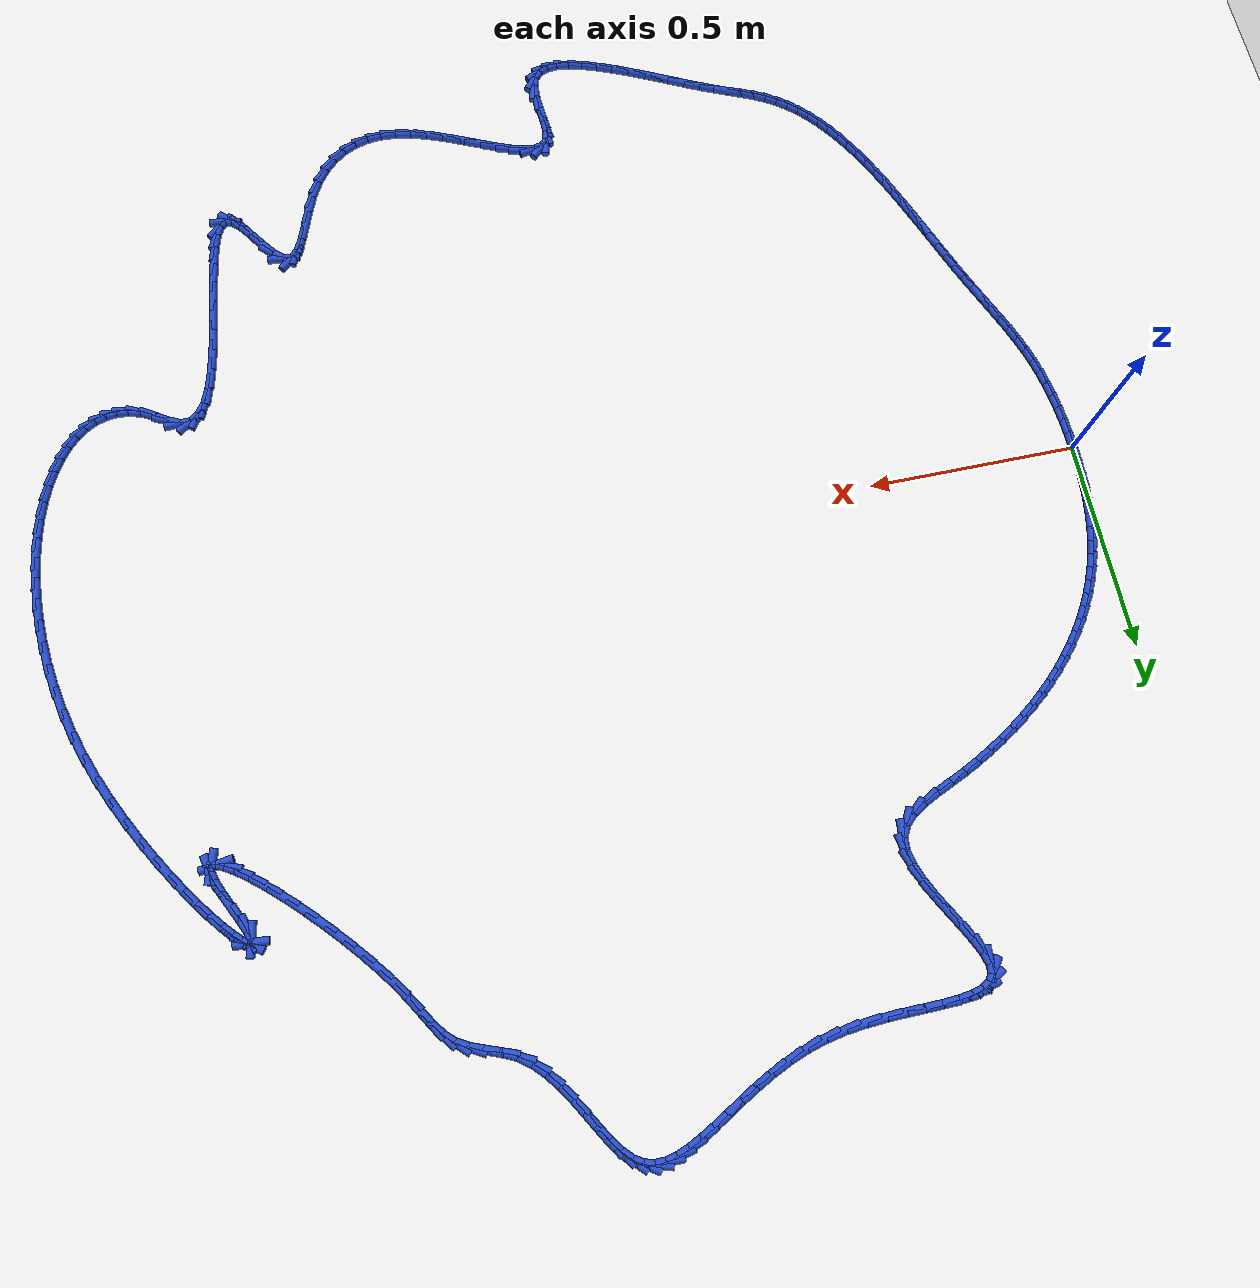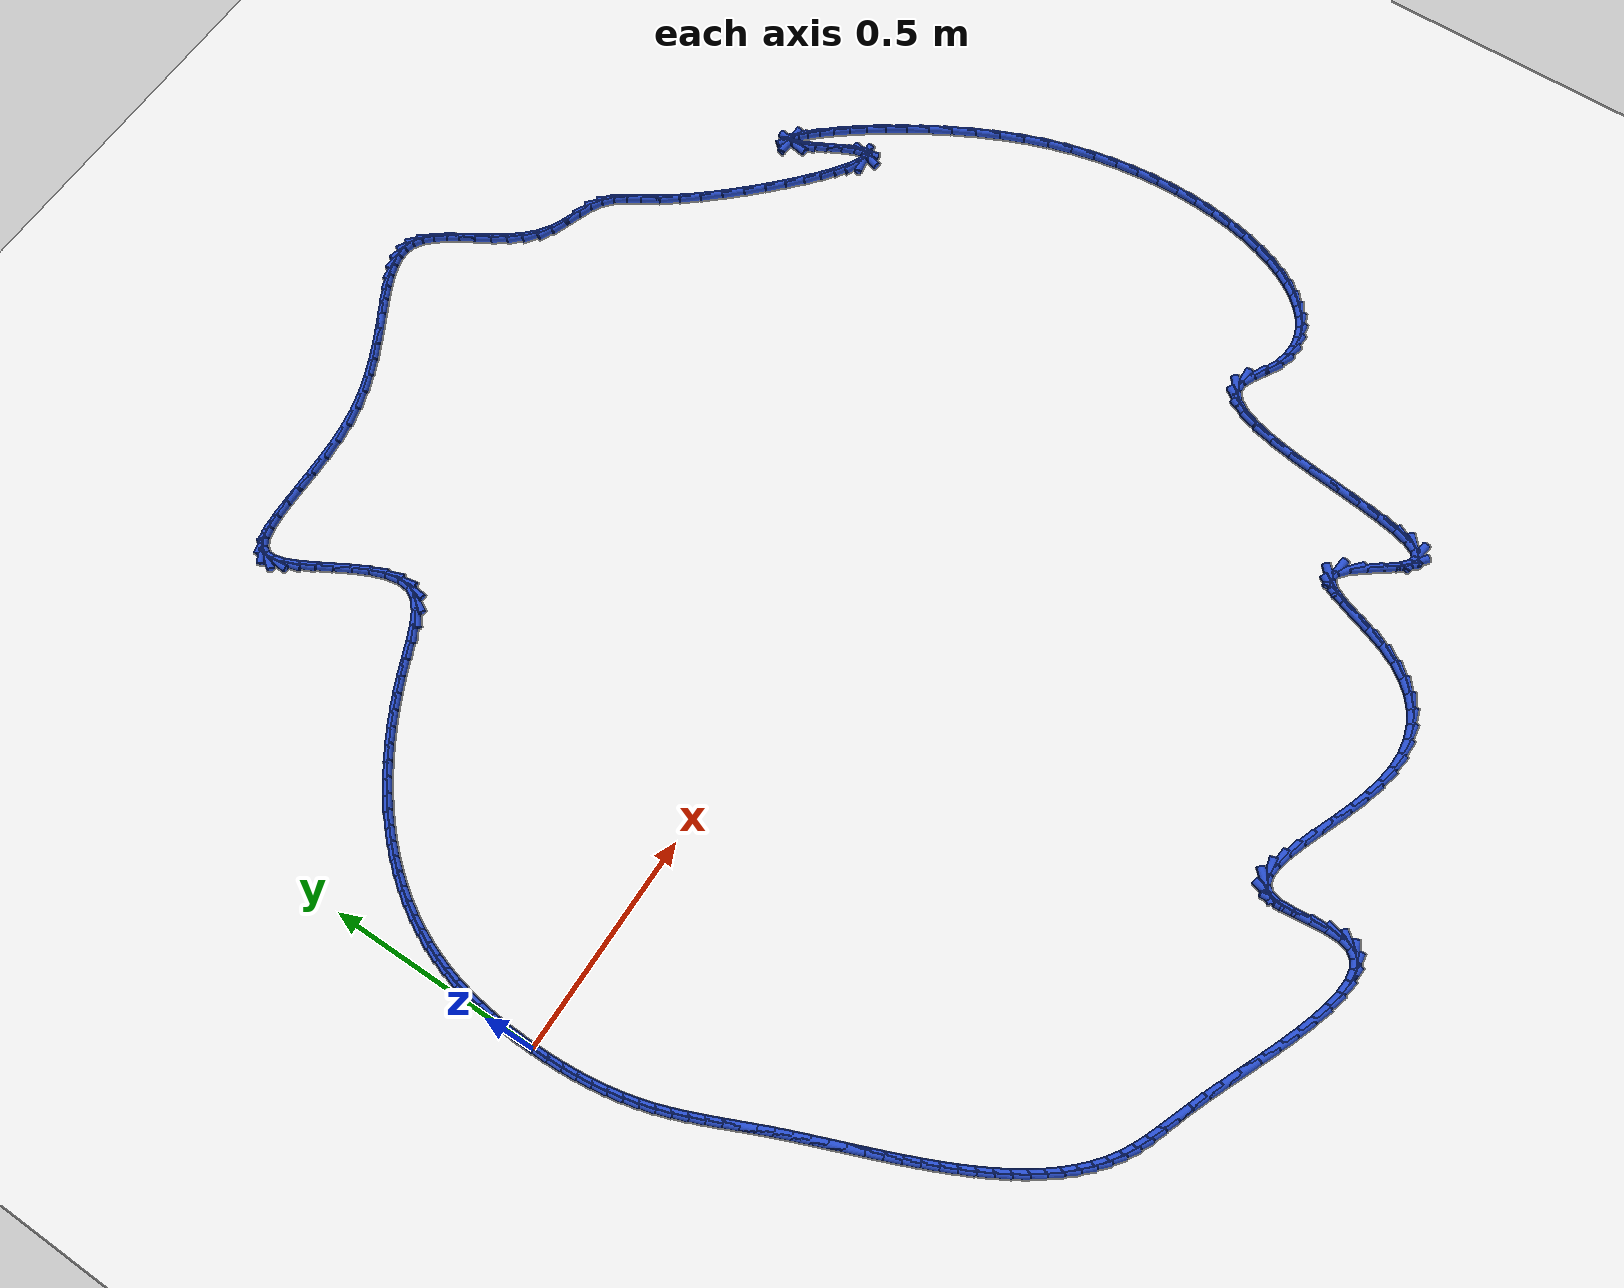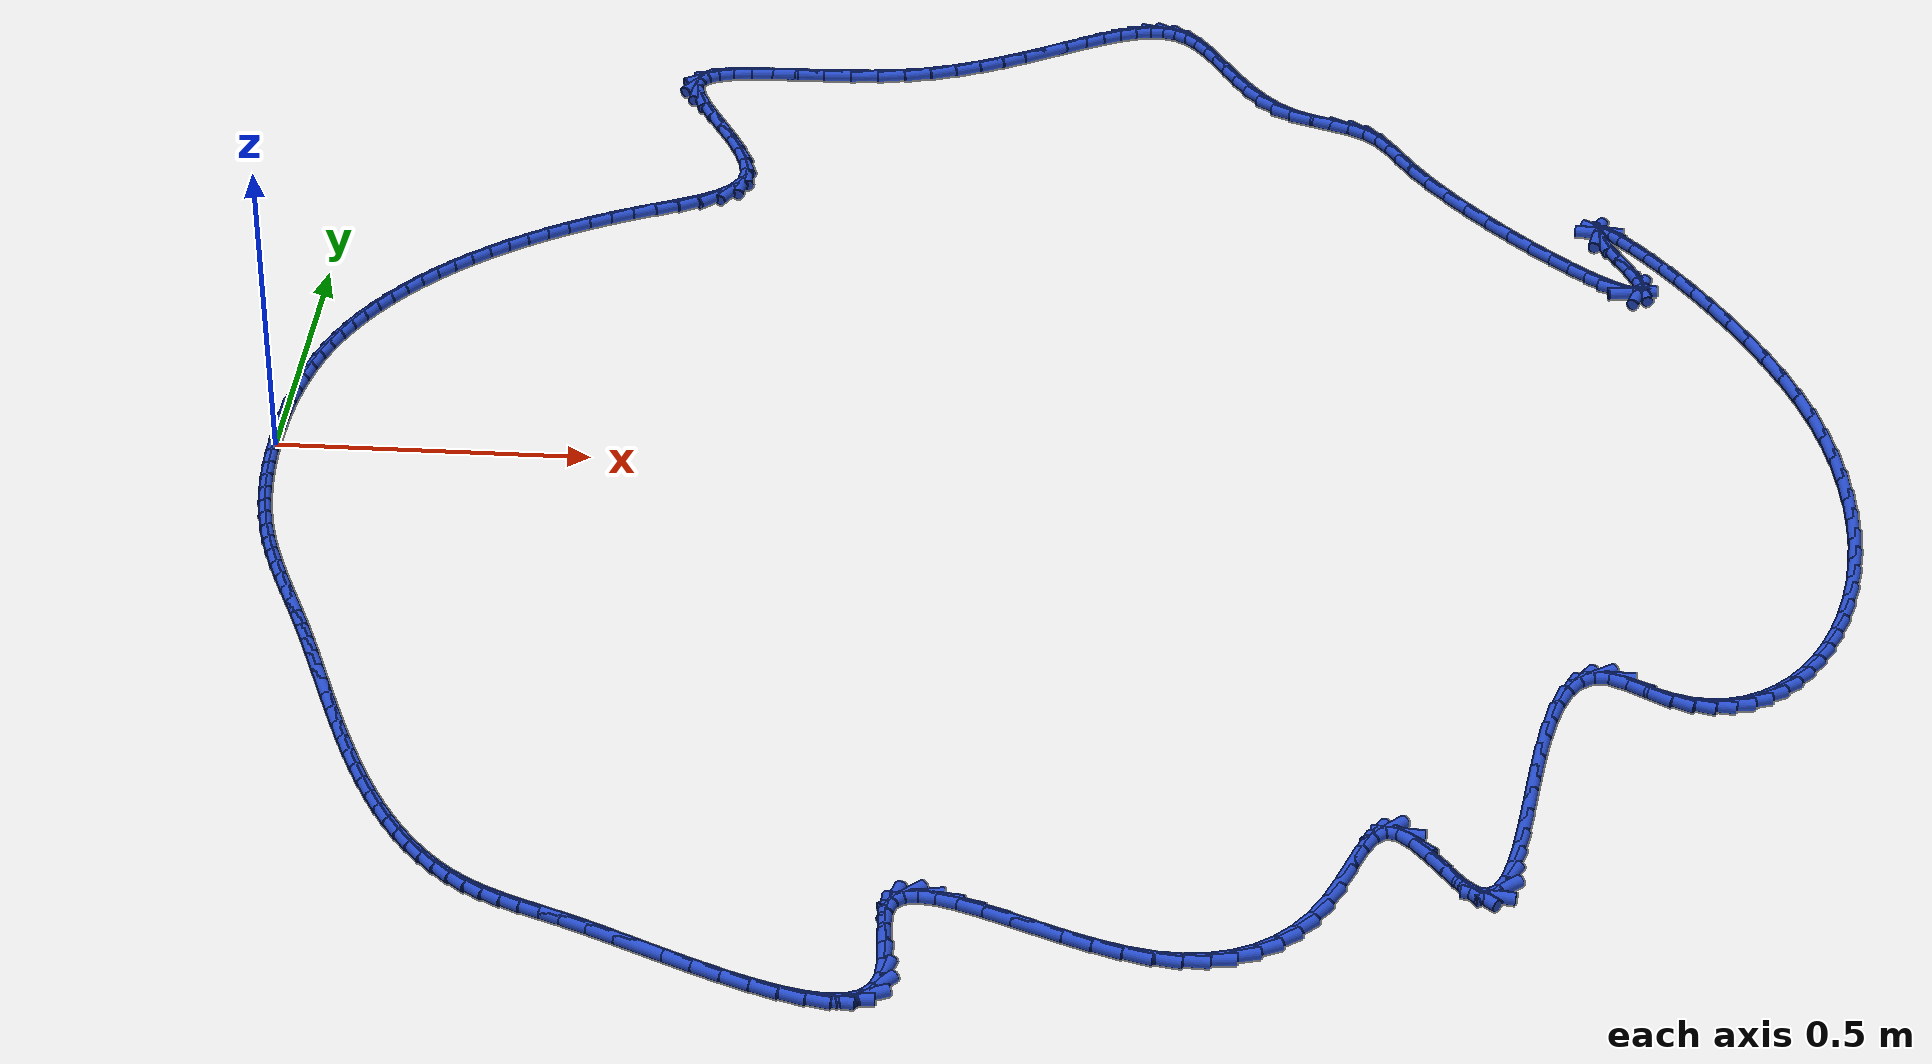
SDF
<sdf version="1.6">
 <world name="default">
  <light name="sun" type="directional">
   <pose>0 0 10 0 -0 0</pose>
   <diffuse>0.8 0.8 0.8 1</diffuse>
   <specular>0.2 0.2 0.2 1</specular>
   <attenuation>
    <range>1000</range>
    <constant>0.9</constant>
    <linear>0.01</linear>
    <quadratic>0.001</quadratic>
   </attenuation>
   <direction>-0.5 0.1 -0.9</direction>
  </light>
  <model name="ground_plane">
   <static>1</static>
   <link name="link">
    <collision name="collision">
     <geometry><plane><normal>0 0 1</normal><size>100 100</size></plane></geometry>
     <surface><friction><ode><mu>100</mu><mu2>50</mu2></ode></friction></surface>
    </collision>
    <visual name="visual">
     <cast_shadows>0</cast_shadows>
     <geometry><plane><normal>0 0 1</normal><size>100 100</size></plane></geometry>
     <material>
      <script><uri>file://media/materials/scripts/gazebo.material</uri><name>Gazebo/WhiteGlow</name></script>
     </material>
    </visual>
   </link>
  </model>
  <gravity>0 0 -9.8</gravity>
  <magnetic_field>6e-06 2.3e-05 -4.2e-05</magnetic_field>
  <atmosphere type="adiabatic"/>
  <physics name="default_physics" default="0" type="ode">
   <max_step_size>0.001</max_step_size>
   <real_time_factor>1</real_time_factor>
   <real_time_update_rate>1000</real_time_update_rate>
  </physics>
  <scene><ambient>0.4 0.4 0.4 1</ambient><background>0.7 0.7 0.7 1</background><shadows>1</shadows></scene>
  <spherical_coordinates>
   <surface_model>EARTH_WGS84</surface_model>
   <latitude_deg>0</latitude_deg>
   <longitude_deg>0</longitude_deg>
   <elevation>0</elevation>
   <heading_deg>0</heading_deg>
  </spherical_coordinates>
  <model name="line">
   <link name="link_0">
    <pose>9.107298248878237e-18 -2.0816681711721685e-17 0.01 0 1.57 1.5601741036166836</pose>
    <collision name="collision">
     <geometry><cylinder><radius>0.01</radius><length>0.08</length></cylinder></geometry>
    </collision>
    <visual name="visual">
     <material>
      <script><name>Gazebo/Blue</name><uri>file://media/materials/scripts/gazebo.material</uri></script>
     </material>
     <geometry><cylinder><radius>0.01</radius><length>0.08</length></cylinder></geometry>
    </visual>
   </link>
   <link name="link_1">
    <pose>0.0003696576563248758 0.034799094972297426 0.01 0 1.57 1.5300016208745044</pose>
    <collision name="collision">
     <geometry><cylinder><radius>0.01</radius><length>0.08</length></cylinder></geometry>
    </collision>
    <visual name="visual">
     <material>
      <script><name>Gazebo/Blue</name><uri>file://media/materials/scripts/gazebo.material</uri></script>
     </material>
     <geometry><cylinder><radius>0.01</radius><length>0.08</length></cylinder></geometry>
    </visual>
   </link>
   <link name="link_2">
    <pose>0.0017872789832463405 0.06952994551020442 0.01 0 1.57 1.4964612532507076</pose>
    <collision name="collision">
     <geometry><cylinder><radius>0.01</radius><length>0.08</length></cylinder></geometry>
    </collision>
    <visual name="visual">
     <material>
      <script><name>Gazebo/Blue</name><uri>file://media/materials/scripts/gazebo.material</uri></script>
     </material>
     <geometry><cylinder><radius>0.01</radius><length>0.08</length></cylinder></geometry>
    </visual>
   </link>
   <link name="link_3">
    <pose>0.004360169303764804 0.10407823398300506 0.01 0 1.57 1.459281129061944</pose>
    <collision name="collision">
     <geometry><cylinder><radius>0.01</radius><length>0.08</length></cylinder></geometry>
    </collision>
    <visual name="visual">
     <material>
      <script><name>Gazebo/Blue</name><uri>file://media/materials/scripts/gazebo.material</uri></script>
     </material>
     <geometry><cylinder><radius>0.01</radius><length>0.08</length></cylinder></geometry>
    </visual>
   </link>
   <link name="link_4">
    <pose>0.008195633940880662 0.13832964275998344 0.01 0 1.57 1.418171307728434</pose>
    <collision name="collision">
     <geometry><cylinder><radius>0.01</radius><length>0.08</length></cylinder></geometry>
    </collision>
    <visual name="visual">
     <material>
      <script><name>Gazebo/Blue</name><uri>file://media/materials/scripts/gazebo.material</uri></script>
     </material>
     <geometry><cylinder><radius>0.01</radius><length>0.08</length></cylinder></geometry>
    </visual>
   </link>
   <link name="link_5">
    <pose>0.013400978217594315 0.17216985421042363 0.01 0 1.57 1.3728354203693114</pose>
    <collision name="collision">
     <geometry><cylinder><radius>0.01</radius><length>0.08</length></cylinder></geometry>
    </collision>
    <visual name="visual">
     <material>
      <script><name>Gazebo/Blue</name><uri>file://media/materials/scripts/gazebo.material</uri></script>
     </material>
     <geometry><cylinder><radius>0.01</radius><length>0.08</length></cylinder></geometry>
    </visual>
   </link>
   <link name="link_6">
    <pose>0.020083507456906152 0.2054845507036096 0.01 0 1.57 1.322988109672323</pose>
    <collision name="collision">
     <geometry><cylinder><radius>0.01</radius><length>0.08</length></cylinder></geometry>
    </collision>
    <visual name="visual">
     <material>
      <script><name>Gazebo/Blue</name><uri>file://media/materials/scripts/gazebo.material</uri></script>
     </material>
     <geometry><cylinder><radius>0.01</radius><length>0.08</length></cylinder></geometry>
    </visual>
   </link>
   <link name="link_7">
    <pose>0.028350526981816584 0.2381594146088255 0.01 0 1.57 1.2686378744577775</pose>
    <collision name="collision">
     <geometry><cylinder><radius>0.01</radius><length>0.08</length></cylinder></geometry>
    </collision>
    <visual name="visual">
     <material>
      <script><name>Gazebo/Blue</name><uri>file://media/materials/scripts/gazebo.material</uri></script>
     </material>
     <geometry><cylinder><radius>0.01</radius><length>0.08</length></cylinder></geometry>
    </visual>
   </link>
   <link name="link_8">
    <pose>0.03830207136026903 0.2700857994772335 0.01 0 1.57 1.2126364870890947</pose>
    <collision name="collision">
     <geometry><cylinder><radius>0.01</radius><length>0.08</length></cylinder></geometry>
    </collision>
    <visual name="visual">
     <material>
      <script><name>Gazebo/Blue</name><uri>file://media/materials/scripts/gazebo.material</uri></script>
     </material>
     <geometry><cylinder><radius>0.01</radius><length>0.08</length></cylinder></geometry>
    </visual>
   </link>
   <link name="link_9">
    <pose>0.049955530400666845 0.30121952169211785 0.01 0 1.57 1.157071261311305</pose>
    <collision name="collision">
     <geometry><cylinder><radius>0.01</radius><length>0.08</length></cylinder></geometry>
    </collision>
    <visual name="visual">
     <material>
      <script><name>Gazebo/Blue</name><uri>file://media/materials/scripts/gazebo.material</uri></script>
     </material>
     <geometry><cylinder><radius>0.01</radius><length>0.08</length></cylinder></geometry>
    </visual>
   </link>
   <link name="link_10">
    <pose>0.06327585301400085 0.3315573014857785 0.01 0 1.57 1.1022400500316027</pose>
    <collision name="collision">
     <geometry><cylinder><radius>0.01</radius><length>0.08</length></cylinder></geometry>
    </collision>
    <visual name="visual">
     <material>
      <script><name>Gazebo/Blue</name><uri>file://media/materials/scripts/gazebo.material</uri></script>
     </material>
     <geometry><cylinder><radius>0.01</radius><length>0.08</length></cylinder></geometry>
    </visual>
   </link>
   <link name="link_11">
    <pose>0.07822715272236105 0.36109651069304693 0.01 0 1.57 1.0483860194654706</pose>
    <collision name="collision">
     <geometry><cylinder><radius>0.01</radius><length>0.08</length></cylinder></geometry>
    </collision>
    <visual name="visual">
     <material>
      <script><name>Gazebo/Blue</name><uri>file://media/materials/scripts/gazebo.material</uri></script>
     </material>
     <geometry><cylinder><radius>0.01</radius><length>0.08</length></cylinder></geometry>
    </visual>
   </link>
   <link name="link_12">
    <pose>0.09477354304783739 0.38983452114875394 0.01 0 1.57 0.9957213868042988</pose>
    <collision name="collision">
     <geometry><cylinder><radius>0.01</radius><length>0.08</length></cylinder></geometry>
    </collision>
    <visual name="visual">
     <material>
      <script><name>Gazebo/Blue</name><uri>file://media/materials/scripts/gazebo.material</uri></script>
     </material>
     <geometry><cylinder><radius>0.01</radius><length>0.08</length></cylinder></geometry>
    </visual>
   </link>
   <link name="link_13">
    <pose>0.1128791375125198 0.4177687046877306 0.01 0 1.57 0.9444236330649348</pose>
    <collision name="collision">
     <geometry><cylinder><radius>0.01</radius><length>0.08</length></cylinder></geometry>
    </collision>
    <visual name="visual">
     <material>
      <script><name>Gazebo/Blue</name><uri>file://media/materials/scripts/gazebo.material</uri></script>
     </material>
     <geometry><cylinder><radius>0.01</radius><length>0.08</length></cylinder></geometry>
    </visual>
   </link>
   <link name="link_14">
    <pose>0.13250804963849813 0.444896433144808 0.01 0 1.57 0.8946338466139881</pose>
    <collision name="collision">
     <geometry><cylinder><radius>0.01</radius><length>0.08</length></cylinder></geometry>
    </collision>
    <visual name="visual">
     <material>
      <script><name>Gazebo/Blue</name><uri>file://media/materials/scripts/gazebo.material</uri></script>
     </material>
     <geometry><cylinder><radius>0.01</radius><length>0.08</length></cylinder></geometry>
    </visual>
   </link>
   <link name="link_15">
    <pose>0.15362439294786245 0.4712150783548174 0.01 0 1.57 0.8464569948748563</pose>
    <collision name="collision">
     <geometry><cylinder><radius>0.01</radius><length>0.08</length></cylinder></geometry>
    </collision>
    <visual name="visual">
     <material>
      <script><name>Gazebo/Blue</name><uri>file://media/materials/scripts/gazebo.material</uri></script>
     </material>
     <geometry><cylinder><radius>0.01</radius><length>0.08</length></cylinder></geometry>
    </visual>
   </link>
   <link name="link_16">
    <pose>0.1761922809627027 0.49672201215258993 0.01 0 1.57 0.7999637765977934</pose>
    <collision name="collision">
     <geometry><cylinder><radius>0.01</radius><length>0.08</length></cylinder></geometry>
    </collision>
    <visual name="visual">
     <material>
      <script><name>Gazebo/Blue</name><uri>file://media/materials/scripts/gazebo.material</uri></script>
     </material>
     <geometry><cylinder><radius>0.01</radius><length>0.08</length></cylinder></geometry>
    </visual>
   </link>
   <link name="link_17">
    <pose>0.20017582720510874 0.5214146063729563 0.01 0 1.57 0.7551936354759681</pose>
    <collision name="collision">
     <geometry><cylinder><radius>0.01</radius><length>0.08</length></cylinder></geometry>
    </collision>
    <visual name="visual">
     <material>
      <script><name>Gazebo/Blue</name><uri>file://media/materials/scripts/gazebo.material</uri></script>
     </material>
     <geometry><cylinder><radius>0.01</radius><length>0.08</length></cylinder></geometry>
    </visual>
   </link>
   <link name="link_18">
    <pose>0.22553914519717053 0.5452902328507481 0.01 0 1.57 0.7121585098736961</pose>
    <collision name="collision">
     <geometry><cylinder><radius>0.01</radius><length>0.08</length></cylinder></geometry>
    </collision>
    <visual name="visual">
     <material>
      <script><name>Gazebo/Blue</name><uri>file://media/materials/scripts/gazebo.material</uri></script>
     </material>
     <geometry><cylinder><radius>0.01</radius><length>0.08</length></cylinder></geometry>
    </visual>
   </link>
   <link name="link_19">
    <pose>0.25224634846097793 0.568346263420796 0.01 0 1.57 0.6708469357460872</pose>
    <collision name="collision">
     <geometry><cylinder><radius>0.01</radius><length>0.08</length></cylinder></geometry>
    </collision>
    <visual name="visual">
     <material>
      <script><name>Gazebo/Blue</name><uri>file://media/materials/scripts/gazebo.material</uri></script>
     </material>
     <geometry><cylinder><radius>0.01</radius><length>0.08</length></cylinder></geometry>
    </visual>
   </link>
   <link name="link_20">
    <pose>0.28026155051862117 0.5905800699179314 0.01 0 1.57 0.6312281904492969</pose>
    <collision name="collision">
     <geometry><cylinder><radius>0.01</radius><length>0.08</length></cylinder></geometry>
    </collision>
    <visual name="visual">
     <material>
      <script><name>Gazebo/Blue</name><uri>file://media/materials/scripts/gazebo.material</uri></script>
     </material>
     <geometry><cylinder><radius>0.01</radius><length>0.08</length></cylinder></geometry>
    </visual>
   </link>
   <link name="link_21">
    <pose>0.3095488648921899 0.6119890241769853 0.01 0 1.57 0.5932562461430482</pose>
    <collision name="collision">
     <geometry><cylinder><radius>0.01</radius><length>0.08</length></cylinder></geometry>
    </collision>
    <visual name="visual">
     <material>
      <script><name>Gazebo/Blue</name><uri>file://media/materials/scripts/gazebo.material</uri></script>
     </material>
     <geometry><cylinder><radius>0.01</radius><length>0.08</length></cylinder></geometry>
    </visual>
   </link>
   <link name="link_22">
    <pose>0.34007240510377407 0.6325704980327886 0.01 0 1.57 0.5568733796082187</pose>
    <collision name="collision">
     <geometry><cylinder><radius>0.01</radius><length>0.08</length></cylinder></geometry>
    </collision>
    <visual name="visual">
     <material>
      <script><name>Gazebo/Blue</name><uri>file://media/materials/scripts/gazebo.material</uri></script>
     </material>
     <geometry><cylinder><radius>0.01</radius><length>0.08</length></cylinder></geometry>
    </visual>
   </link>
   <link name="link_23">
    <pose>0.3717962846754639 0.6523218633201728 0.01 0 1.57 0.5220133525040616</pose>
    <collision name="collision">
     <geometry><cylinder><radius>0.01</radius><length>0.08</length></cylinder></geometry>
    </collision>
    <visual name="visual">
     <material>
      <script><name>Gazebo/Blue</name><uri>file://media/materials/scripts/gazebo.material</uri></script>
     </material>
     <geometry><cylinder><radius>0.01</radius><length>0.08</length></cylinder></geometry>
    </visual>
   </link>
   <link name="link_24">
    <pose>0.404684617129349 0.6712404918739685 0.01 0 1.57 0.48860412883908966</pose>
    <collision name="collision">
     <geometry><cylinder><radius>0.01</radius><length>0.08</length></cylinder></geometry>
    </collision>
    <visual name="visual">
     <material>
      <script><name>Gazebo/Blue</name><uri>file://media/materials/scripts/gazebo.material</uri></script>
     </material>
     <geometry><cylinder><radius>0.01</radius><length>0.08</length></cylinder></geometry>
    </visual>
   </link>
   <link name="link_25">
    <pose>0.4387015159875196 0.6893237555290072 0.01 0 1.57 0.4565701344284632</pose>
    <collision name="collision">
     <geometry><cylinder><radius>0.01</radius><length>0.08</length></cylinder></geometry>
    </collision>
    <visual name="visual">
     <material>
      <script><name>Gazebo/Blue</name><uri>file://media/materials/scripts/gazebo.material</uri></script>
     </material>
     <geometry><cylinder><radius>0.01</radius><length>0.08</length></cylinder></geometry>
    </visual>
   </link>
   <link name="link_26">
    <pose>0.4738110947720653 0.7065690261201196 0.01 0 1.57 0.42595995530069325</pose>
    <collision name="collision">
     <geometry><cylinder><radius>0.01</radius><length>0.08</length></cylinder></geometry>
    </collision>
    <visual name="visual">
     <material>
      <script><name>Gazebo/Blue</name><uri>file://media/materials/scripts/gazebo.material</uri></script>
     </material>
     <geometry><cylinder><radius>0.01</radius><length>0.08</length></cylinder></geometry>
    </visual>
   </link>
   <link name="link_27">
    <pose>0.5099714830338969 0.7229764493643596 0.01 0 1.57 0.41227607151097195</pose>
    <collision name="collision">
     <geometry><cylinder><radius>0.01</radius><length>0.08</length></cylinder></geometry>
    </collision>
    <visual name="visual">
     <material>
      <script><name>Gazebo/Blue</name><uri>file://media/materials/scripts/gazebo.material</uri></script>
     </material>
     <geometry><cylinder><radius>0.01</radius><length>0.08</length></cylinder></geometry>
    </visual>
   </link>
   <link name="link_28">
    <pose>0.5463794437905273 0.7388991040108068 0.01 0 1.57 0.4474354114773365</pose>
    <collision name="collision">
     <geometry><cylinder><radius>0.01</radius><length>0.08</length></cylinder></geometry>
    </collision>
    <visual name="visual">
     <material>
      <script><name>Gazebo/Blue</name><uri>file://media/materials/scripts/gazebo.material</uri></script>
     </material>
     <geometry><cylinder><radius>0.01</radius><length>0.08</length></cylinder></geometry>
    </visual>
   </link>
   <link name="link_29">
    <pose>0.5807325507093745 0.7553850211339979 0.01 0 1.57 0.547441356616262</pose>
    <collision name="collision">
     <geometry><cylinder><radius>0.01</radius><length>0.08</length></cylinder></geometry>
    </collision>
    <visual name="visual">
     <material>
      <script><name>Gazebo/Blue</name><uri>file://media/materials/scripts/gazebo.material</uri></script>
     </material>
     <geometry><cylinder><radius>0.01</radius><length>0.08</length></cylinder></geometry>
    </visual>
   </link>
   <link name="link_30">
    <pose>0.6105532339016472 0.7735634199663679 0.01 0 1.57 0.7440941814532585</pose>
    <collision name="collision">
     <geometry><cylinder><radius>0.01</radius><length>0.08</length></cylinder></geometry>
    </collision>
    <visual name="visual">
     <material>
      <script><name>Gazebo/Blue</name><uri>file://media/materials/scripts/gazebo.material</uri></script>
     </material>
     <geometry><cylinder><radius>0.01</radius><length>0.08</length></cylinder></geometry>
    </visual>
   </link>
   <link name="link_31">
    <pose>0.6333639234785554 0.7945635197403528 0.01 0 1.57 1.0800613581521792</pose>
    <collision name="collision">
     <geometry><cylinder><radius>0.01</radius><length>0.08</length></cylinder></geometry>
    </collision>
    <visual name="visual">
     <material>
      <script><name>Gazebo/Blue</name><uri>file://media/materials/scripts/gazebo.material</uri></script>
     </material>
     <geometry><cylinder><radius>0.01</radius><length>0.08</length></cylinder></geometry>
    </visual>
   </link>
   <link name="link_32">
    <pose>0.6466942165314001 0.8195110774820759 0.01 0 1.57 1.4784292683458358</pose>
    <collision name="collision">
     <geometry><cylinder><radius>0.01</radius><length>0.08</length></cylinder></geometry>
    </collision>
    <visual name="visual">
     <material>
      <script><name>Gazebo/Blue</name><uri>file://media/materials/scripts/gazebo.material</uri></script>
     </material>
     <geometry><cylinder><radius>0.01</radius><length>0.08</length></cylinder></geometry>
    </visual>
   </link>
   <link name="link_33">
    <pose>0.6494150384664269 0.8488838847848167 0.01 0 1.57 -1.3870676291814041</pose>
    <collision name="collision">
     <geometry><cylinder><radius>0.01</radius><length>0.08</length></cylinder></geometry>
    </collision>
    <visual name="visual">
     <material>
      <script><name>Gazebo/Blue</name><uri>file://media/materials/scripts/gazebo.material</uri></script>
     </material>
     <geometry><cylinder><radius>0.01</radius><length>0.08</length></cylinder></geometry>
    </visual>
   </link>
   <link name="link_34">
    <pose>0.6433069420436678 0.8817541579425682 0.01 0 1.57 -1.2231525068888396</pose>
    <collision name="collision">
     <geometry><cylinder><radius>0.01</radius><length>0.08</length></cylinder></geometry>
    </collision>
    <visual name="visual">
     <material>
      <script><name>Gazebo/Blue</name><uri>file://media/materials/scripts/gazebo.material</uri></script>
     </material>
     <geometry><cylinder><radius>0.01</radius><length>0.08</length></cylinder></geometry>
    </visual>
   </link>
   <link name="link_35">
    <pose>0.6305316134239947 0.9170099963062199 0.01 0 1.57 -1.1289269456628908</pose>
    <collision name="collision">
     <geometry><cylinder><radius>0.01</radius><length>0.08</length></cylinder></geometry>
    </collision>
    <visual name="visual">
     <material>
      <script><name>Gazebo/Blue</name><uri>file://media/materials/scripts/gazebo.material</uri></script>
     </material>
     <geometry><cylinder><radius>0.01</radius><length>0.08</length></cylinder></geometry>
    </visual>
   </link>
   <link name="link_36">
    <pose>0.6132507387682797 0.9535394992266615 0.01 0 1.57 -1.0796502497421423</pose>
    <collision name="collision">
     <geometry><cylinder><radius>0.01</radius><length>0.08</length></cylinder></geometry>
    </collision>
    <visual name="visual">
     <material>
      <script><name>Gazebo/Blue</name><uri>file://media/materials/scripts/gazebo.material</uri></script>
     </material>
     <geometry><cylinder><radius>0.01</radius><length>0.08</length></cylinder></geometry>
    </visual>
   </link>
   <link name="link_37">
    <pose>0.5936260042373949 0.9902307660547813 0.01 0 1.57 -1.0647519490854331</pose>
    <collision name="collision">
     <geometry><cylinder><radius>0.01</radius><length>0.08</length></cylinder></geometry>
    </collision>
    <visual name="visual">
     <material>
      <script><name>Gazebo/Blue</name><uri>file://media/materials/scripts/gazebo.material</uri></script>
     </material>
     <geometry><cylinder><radius>0.01</radius><length>0.08</length></cylinder></geometry>
    </visual>
   </link>
   <link name="link_38">
    <pose>0.573819095992212 1.0259718961414699 0.01 0 1.57 -1.0839599957289607</pose>
    <collision name="collision">
     <geometry><cylinder><radius>0.01</radius><length>0.08</length></cylinder></geometry>
    </collision>
    <visual name="visual">
     <material>
      <script><name>Gazebo/Blue</name><uri>file://media/materials/scripts/gazebo.material</uri></script>
     </material>
     <geometry><cylinder><radius>0.01</radius><length>0.08</length></cylinder></geometry>
    </visual>
   </link>
   <link name="link_39">
    <pose>0.5559917001936033 1.0596509888376158 0.01 0 1.57 -1.1490640036105226</pose>
    <collision name="collision">
     <geometry><cylinder><radius>0.01</radius><length>0.08</length></cylinder></geometry>
    </collision>
    <visual name="visual">
     <material>
      <script><name>Gazebo/Blue</name><uri>file://media/materials/scripts/gazebo.material</uri></script>
     </material>
     <geometry><cylinder><radius>0.01</radius><length>0.08</length></cylinder></geometry>
    </visual>
   </link>
   <link name="link_40">
    <pose>0.5423055030024407 1.0901561434941083 0.01 0 1.57 -1.2963062206103946</pose>
    <collision name="collision">
     <geometry><cylinder><radius>0.01</radius><length>0.08</length></cylinder></geometry>
    </collision>
    <visual name="visual">
     <material>
      <script><name>Gazebo/Blue</name><uri>file://media/materials/scripts/gazebo.material</uri></script>
     </material>
     <geometry><cylinder><radius>0.01</radius><length>0.08</length></cylinder></geometry>
    </visual>
   </link>
   <link name="link_41">
    <pose>0.5349221905795961 1.1163754594618365 0.01 0 1.57 1.52173929487831</pose>
    <collision name="collision">
     <geometry><cylinder><radius>0.01</radius><length>0.08</length></cylinder></geometry>
    </collision>
    <visual name="visual">
     <material>
      <script><name>Gazebo/Blue</name><uri>file://media/materials/scripts/gazebo.material</uri></script>
     </material>
     <geometry><cylinder><radius>0.01</radius><length>0.08</length></cylinder></geometry>
    </visual>
   </link>
   <link name="link_42">
    <pose>0.5359462235607795 1.1372330477162387 0.01 0 1.57 0.9906644327643249</pose>
    <collision name="collision">
     <geometry><cylinder><radius>0.01</radius><length>0.08</length></cylinder></geometry>
    </collision>
    <visual name="visual">
     <material>
      <script><name>Gazebo/Blue</name><uri>file://media/materials/scripts/gazebo.material</uri></script>
     </material>
     <geometry><cylinder><radius>0.01</radius><length>0.08</length></cylinder></geometry>
    </visual>
   </link>
   <link name="link_43">
    <pose>0.5460054320084174 1.152582252571409 0.01 0 1.57 0.5319871836952516</pose>
    <collision name="collision">
     <geometry><cylinder><radius>0.01</radius><length>0.08</length></cylinder></geometry>
    </collision>
    <visual name="visual">
     <material>
      <script><name>Gazebo/Blue</name><uri>file://media/materials/scripts/gazebo.material</uri></script>
     </material>
     <geometry><cylinder><radius>0.01</radius><length>0.08</length></cylinder></geometry>
    </visual>
   </link>
   <link name="link_44">
    <pose>0.5641559653012499 1.1632654660527812 0.01 0 1.57 0.2673198881491739</pose>
    <collision name="collision">
     <geometry><cylinder><radius>0.01</radius><length>0.08</length></cylinder></geometry>
    </collision>
    <visual name="visual">
     <material>
      <script><name>Gazebo/Blue</name><uri>file://media/materials/scripts/gazebo.material</uri></script>
     </material>
     <geometry><cylinder><radius>0.01</radius><length>0.08</length></cylinder></geometry>
    </visual>
   </link>
   <link name="link_45">
    <pose>0.5893777140766487 1.1701730692807775 0.01 0 1.57 0.1279195714314564</pose>
    <collision name="collision">
     <geometry><cylinder><radius>0.01</radius><length>0.08</length></cylinder></geometry>
    </collision>
    <visual name="visual">
     <material>
      <script><name>Gazebo/Blue</name><uri>file://media/materials/scripts/gazebo.material</uri></script>
     </material>
     <geometry><cylinder><radius>0.01</radius><length>0.08</length></cylinder></geometry>
    </visual>
   </link>
   <link name="link_46">
    <pose>0.620650568971986 1.1741954433758208 0.01 0 1.57 0.05579082980136638</pose>
    <collision name="collision">
     <geometry><cylinder><radius>0.01</radius><length>0.08</length></cylinder></geometry>
    </collision>
    <visual name="visual">
     <material>
      <script><name>Gazebo/Blue</name><uri>file://media/materials/scripts/gazebo.material</uri></script>
     </material>
     <geometry><cylinder><radius>0.01</radius><length>0.08</length></cylinder></geometry>
    </visual>
   </link>
   <link name="link_47">
    <pose>0.6569544206246336 1.1762229694583328 0.01 0 1.57 0.02289232079759322</pose>
    <collision name="collision">
     <geometry><cylinder><radius>0.01</radius><length>0.08</length></cylinder></geometry>
    </collision>
    <visual name="visual">
     <material>
      <script><name>Gazebo/Blue</name><uri>file://media/materials/scripts/gazebo.material</uri></script>
     </material>
     <geometry><cylinder><radius>0.01</radius><length>0.08</length></cylinder></geometry>
    </visual>
   </link>
   <link name="link_48">
    <pose>0.697269159671963 1.1771460286487352 0.01 0 1.57 0.016369971682927607</pose>
    <collision name="collision">
     <geometry><cylinder><radius>0.01</radius><length>0.08</length></cylinder></geometry>
    </collision>
    <visual name="visual">
     <material>
      <script><name>Gazebo/Blue</name><uri>file://media/materials/scripts/gazebo.material</uri></script>
     </material>
     <geometry><cylinder><radius>0.01</radius><length>0.08</length></cylinder></geometry>
    </visual>
   </link>
   <link name="link_49">
    <pose>0.7405746767513468 1.1778550020674512 0.01 0 1.57 0.03058642708066966</pose>
    <collision name="collision">
     <geometry><cylinder><radius>0.01</radius><length>0.08</length></cylinder></geometry>
    </collision>
    <visual name="visual">
     <material>
      <script><name>Gazebo/Blue</name><uri>file://media/materials/scripts/gazebo.material</uri></script>
     </material>
     <geometry><cylinder><radius>0.01</radius><length>0.08</length></cylinder></geometry>
    </visual>
   </link>
   <link name="link_50">
    <pose>0.7858508625001561 1.179240270834902 0.01 0 1.57 0.06377136231184242</pose>
    <collision name="collision">
     <geometry><cylinder><radius>0.01</radius><length>0.08</length></cylinder></geometry>
    </collision>
    <visual name="visual">
     <material>
      <script><name>Gazebo/Blue</name><uri>file://media/materials/scripts/gazebo.material</uri></script>
     </material>
     <geometry><cylinder><radius>0.01</radius><length>0.08</length></cylinder></geometry>
    </visual>
   </link>
   <link name="link_51">
    <pose>0.8320776075557633 1.1821922160715104 0.01 0 1.57 0.1166545065703392</pose>
    <collision name="collision">
     <geometry><cylinder><radius>0.01</radius><length>0.08</length></cylinder></geometry>
    </collision>
    <visual name="visual">
     <material>
      <script><name>Gazebo/Blue</name><uri>file://media/materials/scripts/gazebo.material</uri></script>
     </material>
     <geometry><cylinder><radius>0.01</radius><length>0.08</length></cylinder></geometry>
    </visual>
   </link>
   <link name="link_52">
    <pose>0.8782348025555402 1.1876012188976983 0.01 0 1.57 0.19184275539186518</pose>
    <collision name="collision">
     <geometry><cylinder><radius>0.01</radius><length>0.08</length></cylinder></geometry>
    </collision>
    <visual name="visual">
     <material>
      <script><name>Gazebo/Blue</name><uri>file://media/materials/scripts/gazebo.material</uri></script>
     </material>
     <geometry><cylinder><radius>0.01</radius><length>0.08</length></cylinder></geometry>
    </visual>
   </link>
   <link name="link_53">
    <pose>0.9233039177754145 1.196355057614738 0.01 0 1.57 0.2810676748567286</pose>
    <collision name="collision">
     <geometry><cylinder><radius>0.01</radius><length>0.08</length></cylinder></geometry>
    </collision>
    <visual name="visual">
     <material>
      <script><name>Gazebo/Blue</name><uri>file://media/materials/scripts/gazebo.material</uri></script>
     </material>
     <geometry><cylinder><radius>0.01</radius><length>0.08</length></cylinder></geometry>
    </visual>
   </link>
   <link name="link_54">
    <pose>0.9665673468203768 1.2088456698768362 0.01 0 1.57 0.3591092523486554</pose>
    <collision name="collision">
     <geometry><cylinder><radius>0.01</radius><length>0.08</length></cylinder></geometry>
    </collision>
    <visual name="visual">
     <material>
      <script><name>Gazebo/Blue</name><uri>file://media/materials/scripts/gazebo.material</uri></script>
     </material>
     <geometry><cylinder><radius>0.01</radius><length>0.08</length></cylinder></geometry>
    </visual>
   </link>
   <link name="link_55">
    <pose>1.0079629256603058 1.2243850007456292 0.01 0 1.57 0.4220027273728106</pose>
    <collision name="collision">
     <geometry><cylinder><radius>0.01</radius><length>0.08</length></cylinder></geometry>
    </collision>
    <visual name="visual">
     <material>
      <script><name>Gazebo/Blue</name><uri>file://media/materials/scripts/gazebo.material</uri></script>
     </material>
     <geometry><cylinder><radius>0.01</radius><length>0.08</length></cylinder></geometry>
    </visual>
   </link>
   <link name="link_56">
    <pose>1.047514754383584 1.2421428552350848 0.01 0 1.57 0.46956852440720714</pose>
    <collision name="collision">
     <geometry><cylinder><radius>0.01</radius><length>0.08</length></cylinder></geometry>
    </collision>
    <visual name="visual">
     <material>
      <script><name>Gazebo/Blue</name><uri>file://media/materials/scripts/gazebo.material</uri></script>
     </material>
     <geometry><cylinder><radius>0.01</radius><length>0.08</length></cylinder></geometry>
    </visual>
   </link>
   <link name="link_57">
    <pose>1.085246933078594 1.2612890383591713 0.01 0 1.57 0.5015427233821299</pose>
    <collision name="collision">
     <geometry><cylinder><radius>0.01</radius><length>0.08</length></cylinder></geometry>
    </collision>
    <visual name="visual">
     <material>
      <script><name>Gazebo/Blue</name><uri>file://media/materials/scripts/gazebo.material</uri></script>
     </material>
     <geometry><cylinder><radius>0.01</radius><length>0.08</length></cylinder></geometry>
    </visual>
   </link>
   <link name="link_58">
    <pose>1.1211835618337176 1.2809933551318569 0.01 0 1.57 0.5171424657023757</pose>
    <collision name="collision">
     <geometry><cylinder><radius>0.01</radius><length>0.08</length></cylinder></geometry>
    </collision>
    <visual name="visual">
     <material>
      <script><name>Gazebo/Blue</name><uri>file://media/materials/scripts/gazebo.material</uri></script>
     </material>
     <geometry><cylinder><radius>0.01</radius><length>0.08</length></cylinder></geometry>
    </visual>
   </link>
   <link name="link_59">
    <pose>1.1553487407373375 1.3004256105671101 0.01 0 1.57 0.5146121025029433</pose>
    <collision name="collision">
     <geometry><cylinder><radius>0.01</radius><length>0.08</length></cylinder></geometry>
    </collision>
    <visual name="visual">
     <material>
      <script><name>Gazebo/Blue</name><uri>file://media/materials/scripts/gazebo.material</uri></script>
     </material>
     <geometry><cylinder><radius>0.01</radius><length>0.08</length></cylinder></geometry>
    </visual>
   </link>
   <link name="link_60">
    <pose>1.1877665698778361 1.3187556096788993 0.01 0 1.57 0.4906445843342437</pose>
    <collision name="collision">
     <geometry><cylinder><radius>0.01</radius><length>0.08</length></cylinder></geometry>
    </collision>
    <visual name="visual">
     <material>
      <script><name>Gazebo/Blue</name><uri>file://media/materials/scripts/gazebo.material</uri></script>
     </material>
     <geometry><cylinder><radius>0.01</radius><length>0.08</length></cylinder></geometry>
    </visual>
   </link>
   <link name="link_61">
    <pose>1.2184611493435957 1.3351531574811926 0.01 0 1.57 0.4395600031045086</pose>
    <collision name="collision">
     <geometry><cylinder><radius>0.01</radius><length>0.08</length></cylinder></geometry>
    </collision>
    <visual name="visual">
     <material>
      <script><name>Gazebo/Blue</name><uri>file://media/materials/scripts/gazebo.material</uri></script>
     </material>
     <geometry><cylinder><radius>0.01</radius><length>0.08</length></cylinder></geometry>
    </visual>
   </link>
   <link name="link_62">
    <pose>1.2474565792229988 1.3487880589879582 0.01 0 1.57 0.3522378732071377</pose>
    <collision name="collision">
     <geometry><cylinder><radius>0.01</radius><length>0.08</length></cylinder></geometry>
    </collision>
    <visual name="visual">
     <material>
      <script><name>Gazebo/Blue</name><uri>file://media/materials/scripts/gazebo.material</uri></script>
     </material>
     <geometry><cylinder><radius>0.01</radius><length>0.08</length></cylinder></geometry>
    </visual>
   </link>
   <link name="link_63">
    <pose>1.2747769596044272 1.3588301192131642 0.01 0 1.57 0.21550030688081537</pose>
    <collision name="collision">
     <geometry><cylinder><radius>0.01</radius><length>0.08</length></cylinder></geometry>
    </collision>
    <visual name="visual">
     <material>
      <script><name>Gazebo/Blue</name><uri>file://media/materials/scripts/gazebo.material</uri></script>
     </material>
     <geometry><cylinder><radius>0.01</radius><length>0.08</length></cylinder></geometry>
    </visual>
   </link>
   <link name="link_64">
    <pose>1.3004463905762635 1.3644491431707793 0.01 0 1.57 0.015213195031420632</pose>
    <collision name="collision">
     <geometry><cylinder><radius>0.01</radius><length>0.08</length></cylinder></geometry>
    </collision>
    <visual name="visual">
     <material>
      <script><name>Gazebo/Blue</name><uri>file://media/materials/scripts/gazebo.material</uri></script>
     </material>
     <geometry><cylinder><radius>0.01</radius><length>0.08</length></cylinder></geometry>
    </visual>
   </link>
   <link name="link_65">
    <pose>1.3244889722268902 1.3648149358747712 0.01 0 1.57 -0.24948968640286232</pose>
    <collision name="collision">
     <geometry><cylinder><radius>0.01</radius><length>0.08</length></cylinder></geometry>
    </collision>
    <visual name="visual">
     <material>
      <script><name>Gazebo/Blue</name><uri>file://media/materials/scripts/gazebo.material</uri></script>
     </material>
     <geometry><cylinder><radius>0.01</radius><length>0.08</length></cylinder></geometry>
    </visual>
   </link>
   <link name="link_66">
    <pose>1.3469288046446897 1.359097302339109 0.01 0 1.57 -0.543616779621756</pose>
    <collision name="collision">
     <geometry><cylinder><radius>0.01</radius><length>0.08</length></cylinder></geometry>
    </collision>
    <visual name="visual">
     <material>
      <script><name>Gazebo/Blue</name><uri>file://media/materials/scripts/gazebo.material</uri></script>
     </material>
     <geometry><cylinder><radius>0.01</radius><length>0.08</length></cylinder></geometry>
    </visual>
   </link>
   <link name="link_67">
    <pose>1.36779480778764 1.3464867941120446 0.01 0 1.57 -0.7815544751937383</pose>
    <collision name="collision">
     <geometry><cylinder><radius>0.01</radius><length>0.08</length></cylinder></geometry>
    </collision>
    <visual name="visual">
     <material>
      <script><name>Gazebo/Blue</name><uri>file://media/materials/scripts/gazebo.material</uri></script>
     </material>
     <geometry><cylinder><radius>0.01</radius><length>0.08</length></cylinder></geometry>
    </visual>
   </link>
   <link name="link_68">
    <pose>1.3873310722021572 1.3271001380047598 0.01 0 1.57 -0.9228962749175372</pose>
    <collision name="collision">
     <geometry><cylinder><radius>0.01</radius><length>0.08</length></cylinder></geometry>
    </collision>
    <visual name="visual">
     <material>
      <script><name>Gazebo/Blue</name><uri>file://media/materials/scripts/gazebo.material</uri></script>
     </material>
     <geometry><cylinder><radius>0.01</radius><length>0.08</length></cylinder></geometry>
    </visual>
   </link>
   <link name="link_69">
    <pose>1.406078440249268 1.3023313924187676 0.01 0 1.57 -0.9971311463169636</pose>
    <collision name="collision">
     <geometry><cylinder><radius>0.01</radius><length>0.08</length></cylinder></geometry>
    </collision>
    <visual name="visual">
     <material>
      <script><name>Gazebo/Blue</name><uri>file://media/materials/scripts/gazebo.material</uri></script>
     </material>
     <geometry><cylinder><radius>0.01</radius><length>0.08</length></cylinder></geometry>
    </visual>
   </link>
   <link name="link_70">
    <pose>1.4245994208024282 1.2736678765863927 0.01 0 1.57 -1.0253156294237578</pose>
    <collision name="collision">
     <geometry><cylinder><radius>0.01</radius><length>0.08</length></cylinder></geometry>
    </collision>
    <visual name="visual">
     <material>
      <script><name>Gazebo/Blue</name><uri>file://media/materials/scripts/gazebo.material</uri></script>
     </material>
     <geometry><cylinder><radius>0.01</radius><length>0.08</length></cylinder></geometry>
    </visual>
   </link>
   <link name="link_71">
    <pose>1.443456522735092 1.2425969097399592 0.01 0 1.57 -1.017580651424875</pose>
    <collision name="collision">
     <geometry><cylinder><radius>0.01</radius><length>0.08</length></cylinder></geometry>
    </collision>
    <visual name="visual">
     <material>
      <script><name>Gazebo/Blue</name><uri>file://media/materials/scripts/gazebo.material</uri></script>
     </material>
     <geometry><cylinder><radius>0.01</radius><length>0.08</length></cylinder></geometry>
    </visual>
   </link>
   <link name="link_72">
    <pose>1.4632122549207132 1.2106058111117899 0.01 0 1.57 -0.9769213736126775</pose>
    <collision name="collision">
     <geometry><cylinder><radius>0.01</radius><length>0.08</length></cylinder></geometry>
    </collision>
    <visual name="visual">
     <material>
      <script><name>Gazebo/Blue</name><uri>file://media/materials/scripts/gazebo.material</uri></script>
     </material>
     <geometry><cylinder><radius>0.01</radius><length>0.08</length></cylinder></geometry>
    </visual>
   </link>
   <link name="link_73">
    <pose>1.4844291262327463 1.1791818999342094 0.01 0 1.57 -0.9013721528112686</pose>
    <collision name="collision">
     <geometry><cylinder><radius>0.01</radius><length>0.08</length></cylinder></geometry>
    </collision>
    <visual name="visual">
     <material>
      <script><name>Gazebo/Blue</name><uri>file://media/materials/scripts/gazebo.material</uri></script>
     </material>
     <geometry><cylinder><radius>0.01</radius><length>0.08</length></cylinder></geometry>
    </visual>
   </link>
   <link name="link_74">
    <pose>1.507669645544646 1.1498124954395406 0.01 0 1.57 -0.7854156332886453</pose>
    <collision name="collision">
     <geometry><cylinder><radius>0.01</radius><length>0.08</length></cylinder></geometry>
    </collision>
    <visual name="visual">
     <material>
      <script><name>Gazebo/Blue</name><uri>file://media/materials/scripts/gazebo.material</uri></script>
     </material>
     <geometry><cylinder><radius>0.01</radius><length>0.08</length></cylinder></geometry>
    </visual>
   </link>
   <link name="link_75">
    <pose>1.5334963217298676 1.1239849168601084 0.01 0 1.57 -0.6225711455977114</pose>
    <collision name="collision">
     <geometry><cylinder><radius>0.01</radius><length>0.08</length></cylinder></geometry>
    </collision>
    <visual name="visual">
     <material>
      <script><name>Gazebo/Blue</name><uri>file://media/materials/scripts/gazebo.material</uri></script>
     </material>
     <geometry><cylinder><radius>0.01</radius><length>0.08</length></cylinder></geometry>
    </visual>
   </link>
   <link name="link_76">
    <pose>1.5624716631783515 1.1031864827021176 0.01 0 1.57 -0.43891997333617555</pose>
    <collision name="collision">
     <geometry><cylinder><radius>0.01</radius><length>0.08</length></cylinder></geometry>
    </collision>
    <visual name="visual">
     <material>
      <script><name>Gazebo/Blue</name><uri>file://media/materials/scripts/gazebo.material</uri></script>
     </material>
     <geometry><cylinder><radius>0.01</radius><length>0.08</length></cylinder></geometry>
    </visual>
   </link>
   <link name="link_77">
    <pose>1.5946188676974309 1.0880945982146644 0.01 0 1.57 -0.34250005749897494</pose>
    <collision name="collision">
     <geometry><cylinder><radius>0.01</radius><length>0.08</length></cylinder></geometry>
    </collision>
    <visual name="visual">
     <material>
      <script><name>Gazebo/Blue</name><uri>file://media/materials/scripts/gazebo.material</uri></script>
     </material>
     <geometry><cylinder><radius>0.01</radius><length>0.08</length></cylinder></geometry>
    </visual>
   </link>
   <link name="link_78">
    <pose>1.6278659835233964 1.0762402638331263 0.01 0 1.57 -0.35704056017298813</pose>
    <collision name="collision">
     <geometry><cylinder><radius>0.01</radius><length>0.08</length></cylinder></geometry>
    </collision>
    <visual name="visual">
     <material>
      <script><name>Gazebo/Blue</name><uri>file://media/materials/scripts/gazebo.material</uri></script>
     </material>
     <geometry><cylinder><radius>0.01</radius><length>0.08</length></cylinder></geometry>
    </visual>
   </link>
   <link name="link_79">
    <pose>1.659632350404784 1.0643905236354068 0.01 0 1.57 -0.49813076466831757</pose>
    <collision name="collision">
     <geometry><cylinder><radius>0.01</radius><length>0.08</length></cylinder></geometry>
    </collision>
    <visual name="visual">
     <material>
      <script><name>Gazebo/Blue</name><uri>file://media/materials/scripts/gazebo.material</uri></script>
     </material>
     <geometry><cylinder><radius>0.01</radius><length>0.08</length></cylinder></geometry>
    </visual>
   </link>
   <link name="link_80">
    <pose>1.6873449093801414 1.0493182763352142 0.01 0 1.57 -0.7351223487382783</pose>
    <collision name="collision">
     <geometry><cylinder><radius>0.01</radius><length>0.08</length></cylinder></geometry>
    </collision>
    <visual name="visual">
     <material>
      <script><name>Gazebo/Blue</name><uri>file://media/materials/scripts/gazebo.material</uri></script>
     </material>
     <geometry><cylinder><radius>0.01</radius><length>0.08</length></cylinder></geometry>
    </visual>
   </link>
   <link name="link_81">
    <pose>1.709897689264707 1.0289263952440504 0.01 0 1.57 -0.9151074802155217</pose>
    <collision name="collision">
     <geometry><cylinder><radius>0.01</radius><length>0.08</length></cylinder></geometry>
    </collision>
    <visual name="visual">
     <material>
      <script><name>Gazebo/Blue</name><uri>file://media/materials/scripts/gazebo.material</uri></script>
     </material>
     <geometry><cylinder><radius>0.01</radius><length>0.08</length></cylinder></geometry>
    </visual>
   </link>
   <link name="link_82">
    <pose>1.729389769618927 1.0035863352976855 0.01 0 1.57 -1.001107841980413</pose>
    <collision name="collision">
     <geometry><cylinder><radius>0.01</radius><length>0.08</length></cylinder></geometry>
    </collision>
    <visual name="visual">
     <material>
      <script><name>Gazebo/Blue</name><uri>file://media/materials/scripts/gazebo.material</uri></script>
     </material>
     <geometry><cylinder><radius>0.01</radius><length>0.08</length></cylinder></geometry>
    </visual>
   </link>
   <link name="link_83">
    <pose>1.7483435154016116 0.9739955726525475 0.01 0 1.57 -1.0073780470392955</pose>
    <collision name="collision">
     <geometry><cylinder><radius>0.01</radius><length>0.08</length></cylinder></geometry>
    </collision>
    <visual name="visual">
     <material>
      <script><name>Gazebo/Blue</name><uri>file://media/materials/scripts/gazebo.material</uri></script>
     </material>
     <geometry><cylinder><radius>0.01</radius><length>0.08</length></cylinder></geometry>
    </visual>
   </link>
   <link name="link_84">
    <pose>1.7692812915715714 0.9408515834650654 0.01 0 1.57 -0.9598930305768948</pose>
    <collision name="collision">
     <geometry><cylinder><radius>0.01</radius><length>0.08</length></cylinder></geometry>
    </collision>
    <visual name="visual">
     <material>
      <script><name>Gazebo/Blue</name><uri>file://media/materials/scripts/gazebo.material</uri></script>
     </material>
     <geometry><cylinder><radius>0.01</radius><length>0.08</length></cylinder></geometry>
    </visual>
   </link>
   <link name="link_85">
    <pose>1.7944791749677402 0.9048681912870554 0.01 0 1.57 -0.9090172277173932</pose>
    <collision name="collision">
     <geometry><cylinder><radius>0.01</radius><length>0.08</length></cylinder></geometry>
    </collision>
    <visual name="visual">
     <material>
      <script><name>Gazebo/Blue</name><uri>file://media/materials/scripts/gazebo.material</uri></script>
     </material>
     <geometry><cylinder><radius>0.01</radius><length>0.08</length></cylinder></geometry>
    </visual>
   </link>
   <link name="link_86">
    <pose>1.8240528220639336 0.8669026177600696 0.01 0 1.57 -0.8695590634977227</pose>
    <collision name="collision">
     <geometry><cylinder><radius>0.01</radius><length>0.08</length></cylinder></geometry>
    </collision>
    <visual name="visual">
     <material>
      <script><name>Gazebo/Blue</name><uri>file://media/materials/scripts/gazebo.material</uri></script>
     </material>
     <geometry><cylinder><radius>0.01</radius><length>0.08</length></cylinder></geometry>
    </visual>
   </link>
   <link name="link_87">
    <pose>1.8569983403884702 0.8278863946843391 0.01 0 1.57 -0.8368136957337593</pose>
    <collision name="collision">
     <geometry><cylinder><radius>0.01</radius><length>0.08</length></cylinder></geometry>
    </collision>
    <visual name="visual">
     <material>
      <script><name>Gazebo/Blue</name><uri>file://media/materials/scripts/gazebo.material</uri></script>
     </material>
     <geometry><cylinder><radius>0.01</radius><length>0.08</length></cylinder></geometry>
    </visual>
   </link>
   <link name="link_88">
    <pose>1.8923023691118148 0.7887516823231726 0.01 0 1.57 -0.8076948305001164</pose>
    <collision name="collision">
     <geometry><cylinder><radius>0.01</radius><length>0.08</length></cylinder></geometry>
    </collision>
    <visual name="visual">
     <material>
      <script><name>Gazebo/Blue</name><uri>file://media/materials/scripts/gazebo.material</uri></script>
     </material>
     <geometry><cylinder><radius>0.01</radius><length>0.08</length></cylinder></geometry>
    </visual>
   </link>
   <link name="link_89">
    <pose>1.9289515474044339 0.7504306409398774 0.01 0 1.57 -0.7798819336224009</pose>
    <collision name="collision">
     <geometry><cylinder><radius>0.01</radius><length>0.08</length></cylinder></geometry>
    </collision>
    <visual name="visual">
     <material>
      <script><name>Gazebo/Blue</name><uri>file://media/materials/scripts/gazebo.material</uri></script>
     </material>
     <geometry><cylinder><radius>0.01</radius><length>0.08</length></cylinder></geometry>
    </visual>
   </link>
   <link name="link_90">
    <pose>1.96593251443679 0.7138554307977619 0.01 0 1.57 -0.7511908256508534</pose>
    <collision name="collision">
     <geometry><cylinder><radius>0.01</radius><length>0.08</length></cylinder></geometry>
    </collision>
    <visual name="visual">
     <material>
      <script><name>Gazebo/Blue</name><uri>file://media/materials/scripts/gazebo.material</uri></script>
     </material>
     <geometry><cylinder><radius>0.01</radius><length>0.08</length></cylinder></geometry>
    </visual>
   </link>
   <link name="link_91">
    <pose>2.0022319093793493 0.679958212160134 0.01 0 1.57 -0.718963581378068</pose>
    <collision name="collision">
     <geometry><cylinder><radius>0.01</radius><length>0.08</length></cylinder></geometry>
    </collision>
    <visual name="visual">
     <material>
      <script><name>Gazebo/Blue</name><uri>file://media/materials/scripts/gazebo.material</uri></script>
     </material>
     <geometry><cylinder><radius>0.01</radius><length>0.08</length></cylinder></geometry>
    </visual>
   </link>
   <link name="link_92">
    <pose>2.036836371402577 0.6496711452903022 0.01 0 1.57 -0.679081011371354</pose>
    <collision name="collision">
     <geometry><cylinder><radius>0.01</radius><length>0.08</length></cylinder></geometry>
    </collision>
    <visual name="visual">
     <material>
      <script><name>Gazebo/Blue</name><uri>file://media/materials/scripts/gazebo.material</uri></script>
     </material>
     <geometry><cylinder><radius>0.01</radius><length>0.08</length></cylinder></geometry>
    </visual>
   </link>
   <link name="link_93">
    <pose>2.0687325396769367 0.6239263904515748 0.01 0 1.57 -0.6236637442712122</pose>
    <collision name="collision">
     <geometry><cylinder><radius>0.01</radius><length>0.08</length></cylinder></geometry>
    </collision>
    <visual name="visual">
     <material>
      <script><name>Gazebo/Blue</name><uri>file://media/materials/scripts/gazebo.material</uri></script>
     </material>
     <geometry><cylinder><radius>0.01</radius><length>0.08</length></cylinder></geometry>
    </visual>
   </link>
   <link name="link_94">
    <pose>2.096907053372894 0.6036561079072594 0.01 0 1.57 -0.5341203534777037</pose>
    <collision name="collision">
     <geometry><cylinder><radius>0.01</radius><length>0.08</length></cylinder></geometry>
    </collision>
    <visual name="visual">
     <material>
      <script><name>Gazebo/Blue</name><uri>file://media/materials/scripts/gazebo.material</uri></script>
     </material>
     <geometry><cylinder><radius>0.01</radius><length>0.08</length></cylinder></geometry>
    </visual>
   </link>
   <link name="link_95">
    <pose>2.120346551660913 0.5897924579206644 0.01 0 1.57 -0.35334248293835285</pose>
    <collision name="collision">
     <geometry><cylinder><radius>0.01</radius><length>0.08</length></cylinder></geometry>
    </collision>
    <visual name="visual">
     <material>
      <script><name>Gazebo/Blue</name><uri>file://media/materials/scripts/gazebo.material</uri></script>
     </material>
     <geometry><cylinder><radius>0.01</radius><length>0.08</length></cylinder></geometry>
    </visual>
   </link>
   <link name="link_96">
    <pose>2.1380376737114593 0.5832676007550979 0.01 0 1.57 0.15842279414602378</pose>
    <collision name="collision">
     <geometry><cylinder><radius>0.01</radius><length>0.08</length></cylinder></geometry>
    </collision>
    <visual name="visual">
     <material>
      <script><name>Gazebo/Blue</name><uri>file://media/materials/scripts/gazebo.material</uri></script>
     </material>
     <geometry><cylinder><radius>0.01</radius><length>0.08</length></cylinder></geometry>
    </visual>
   </link>
   <link name="link_97">
    <pose>2.1489670586949967 0.5850136966738678 0.01 0 1.57 1.2903075884243163</pose>
    <collision name="collision">
     <geometry><cylinder><radius>0.01</radius><length>0.08</length></cylinder></geometry>
    </collision>
    <visual name="visual">
     <material>
      <script><name>Gazebo/Blue</name><uri>file://media/materials/scripts/gazebo.material</uri></script>
     </material>
     <geometry><cylinder><radius>0.01</radius><length>0.08</length></cylinder></geometry>
    </visual>
   </link>
   <link name="link_98">
    <pose>2.1521213457819908 0.5959629059402827 0.01 0 1.57 -1.3104863206941457</pose>
    <collision name="collision">
     <geometry><cylinder><radius>0.01</radius><length>0.08</length></cylinder></geometry>
    </collision>
    <visual name="visual">
     <material>
      <script><name>Gazebo/Blue</name><uri>file://media/materials/scripts/gazebo.material</uri></script>
     </material>
     <geometry><cylinder><radius>0.01</radius><length>0.08</length></cylinder></geometry>
    </visual>
   </link>
   <link name="link_99">
    <pose>2.146513544136977 0.6170168863067343 0.01 0 1.57 -1.147410677020228</pose>
    <collision name="collision">
     <geometry><cylinder><radius>0.01</radius><length>0.08</length></cylinder></geometry>
    </collision>
    <visual name="visual">
     <material>
      <script><name>Gazebo/Blue</name><uri>file://media/materials/scripts/gazebo.material</uri></script>
     </material>
     <geometry><cylinder><radius>0.01</radius><length>0.08</length></cylinder></geometry>
    </visual>
   </link>
   <link name="link_100">
    <pose>2.133055802047664 0.646880536903684 0.01 0 1.57 -1.098142254481773</pose>
    <collision name="collision">
     <geometry><cylinder><radius>0.01</radius><length>0.08</length></cylinder></geometry>
    </collision>
    <visual name="visual">
     <material>
      <script><name>Gazebo/Blue</name><uri>file://media/materials/scripts/gazebo.material</uri></script>
     </material>
     <geometry><cylinder><radius>0.01</radius><length>0.08</length></cylinder></geometry>
    </visual>
   </link>
   <link name="link_101">
    <pose>2.115802269322939 0.680624363336891 0.01 0 1.57 -1.0942859305780233</pose>
    <collision name="collision">
     <geometry><cylinder><radius>0.01</radius><length>0.08</length></cylinder></geometry>
    </collision>
    <visual name="visual">
     <material>
      <script><name>Gazebo/Blue</name><uri>file://media/materials/scripts/gazebo.material</uri></script>
     </material>
     <geometry><cylinder><radius>0.01</radius><length>0.08</length></cylinder></geometry>
    </visual>
   </link>
   <link name="link_102">
    <pose>2.0991019637999044 0.7129777935757197 0.01 0 1.57 -1.1392249426378287</pose>
    <collision name="collision">
     <geometry><cylinder><radius>0.01</radius><length>0.08</length></cylinder></geometry>
    </collision>
    <visual name="visual">
     <material>
      <script><name>Gazebo/Blue</name><uri>file://media/materials/scripts/gazebo.material</uri></script>
     </material>
     <geometry><cylinder><radius>0.01</radius><length>0.08</length></cylinder></geometry>
    </visual>
   </link>
   <link name="link_103">
    <pose>2.0872305249874774 0.7387558881019959 0.01 0 1.57 -1.279096027633235</pose>
    <collision name="collision">
     <geometry><cylinder><radius>0.01</radius><length>0.08</length></cylinder></geometry>
    </collision>
    <visual name="visual">
     <material>
      <script><name>Gazebo/Blue</name><uri>file://media/materials/scripts/gazebo.material</uri></script>
     </material>
     <geometry><cylinder><radius>0.01</radius><length>0.08</length></cylinder></geometry>
    </visual>
   </link>
   <link name="link_104">
    <pose>2.0822435249752345 0.7553645261807754 0.01 0 1.57 1.3953218204497277</pose>
    <collision name="collision">
     <geometry><cylinder><radius>0.01</radius><length>0.08</length></cylinder></geometry>
    </collision>
    <visual name="visual">
     <material>
      <script><name>Gazebo/Blue</name><uri>file://media/materials/scripts/gazebo.material</uri></script>
     </material>
     <geometry><cylinder><radius>0.01</radius><length>0.08</length></cylinder></geometry>
    </visual>
   </link>
   <link name="link_105">
    <pose>2.083632964788153 0.7632012746305934 0.01 0 1.57 -0.052128278619345436</pose>
    <collision name="collision">
     <geometry><cylinder><radius>0.01</radius><length>0.08</length></cylinder></geometry>
    </collision>
    <visual name="visual">
     <material>
      <script><name>Gazebo/Blue</name><uri>file://media/materials/scripts/gazebo.material</uri></script>
     </material>
     <geometry><cylinder><radius>0.01</radius><length>0.08</length></cylinder></geometry>
    </visual>
   </link>
   <link name="link_106">
    <pose>2.09074832035731 0.7628300270612945 0.01 0 1.57 -0.5816257732908231</pose>
    <collision name="collision">
     <geometry><cylinder><radius>0.01</radius><length>0.08</length></cylinder></geometry>
    </collision>
    <visual name="visual">
     <material>
      <script><name>Gazebo/Blue</name><uri>file://media/materials/scripts/gazebo.material</uri></script>
     </material>
     <geometry><cylinder><radius>0.01</radius><length>0.08</length></cylinder></geometry>
    </visual>
   </link>
   <link name="link_107">
    <pose>2.1029390676137845 0.7548146770827261 0.01 0 1.57 -0.7375004254737567</pose>
    <collision name="collision">
     <geometry><cylinder><radius>0.01</radius><length>0.08</length></cylinder></geometry>
    </collision>
    <visual name="visual">
     <material>
      <script><name>Gazebo/Blue</name><uri>file://media/materials/scripts/gazebo.material</uri></script>
     </material>
     <geometry><cylinder><radius>0.01</radius><length>0.08</length></cylinder></geometry>
    </visual>
   </link>
   <link name="link_108">
    <pose>2.1195546824886535 0.7397191183047334 0.01 0 1.57 -0.8144819182985862</pose>
    <collision name="collision">
     <geometry><cylinder><radius>0.01</radius><length>0.08</length></cylinder></geometry>
    </collision>
    <visual name="visual">
     <material>
      <script><name>Gazebo/Blue</name><uri>file://media/materials/scripts/gazebo.material</uri></script>
     </material>
     <geometry><cylinder><radius>0.01</radius><length>0.08</length></cylinder></geometry>
    </visual>
   </link>
   <link name="link_109">
    <pose>2.139944640912995 0.718107244337162 0.01 0 1.57 -0.8645330759963723</pose>
    <collision name="collision">
     <geometry><cylinder><radius>0.01</radius><length>0.08</length></cylinder></geometry>
    </collision>
    <visual name="visual">
     <material>
      <script><name>Gazebo/Blue</name><uri>file://media/materials/scripts/gazebo.material</uri></script>
     </material>
     <geometry><cylinder><radius>0.01</radius><length>0.08</length></cylinder></geometry>
    </visual>
   </link>
   <link name="link_110">
    <pose>2.163458418817886 0.6905429487898582 0.01 0 1.57 -0.9030364428914875</pose>
    <collision name="collision">
     <geometry><cylinder><radius>0.01</radius><length>0.08</length></cylinder></geometry>
    </collision>
    <visual name="visual">
     <material>
      <script><name>Gazebo/Blue</name><uri>file://media/materials/scripts/gazebo.material</uri></script>
     </material>
     <geometry><cylinder><radius>0.01</radius><length>0.08</length></cylinder></geometry>
    </visual>
   </link>
   <link name="link_111">
    <pose>2.189445492134407 0.6575901252726681 0.01 0 1.57 -0.9362188348726279</pose>
    <collision name="collision">
     <geometry><cylinder><radius>0.01</radius><length>0.08</length></cylinder></geometry>
    </collision>
    <visual name="visual">
     <material>
      <script><name>Gazebo/Blue</name><uri>file://media/materials/scripts/gazebo.material</uri></script>
     </material>
     <geometry><cylinder><radius>0.01</radius><length>0.08</length></cylinder></geometry>
    </visual>
   </link>
   <link name="link_112">
    <pose>2.2172553367936336 0.6198126673954372 0.01 0 1.57 -0.9672044953026869</pose>
    <collision name="collision">
     <geometry><cylinder><radius>0.01</radius><length>0.08</length></cylinder></geometry>
    </collision>
    <visual name="visual">
     <material>
      <script><name>Gazebo/Blue</name><uri>file://media/materials/scripts/gazebo.material</uri></script>
     </material>
     <geometry><cylinder><radius>0.01</radius><length>0.08</length></cylinder></geometry>
    </visual>
   </link>
   <link name="link_113">
    <pose>2.2462374287266447 0.5777744687680118 0.01 0 1.57 -0.9978713451272625</pose>
    <collision name="collision">
     <geometry><cylinder><radius>0.01</radius><length>0.08</length></cylinder></geometry>
    </collision>
    <visual name="visual">
     <material>
      <script><name>Gazebo/Blue</name><uri>file://media/materials/scripts/gazebo.material</uri></script>
     </material>
     <geometry><cylinder><radius>0.01</radius><length>0.08</length></cylinder></geometry>
    </visual>
   </link>
   <link name="link_114">
    <pose>2.275741243864518 0.5320394230002377 0.01 0 1.57 -1.029561482406547</pose>
    <collision name="collision">
     <geometry><cylinder><radius>0.01</radius><length>0.08</length></cylinder></geometry>
    </collision>
    <visual name="visual">
     <material>
      <script><name>Gazebo/Blue</name><uri>file://media/materials/scripts/gazebo.material</uri></script>
     </material>
     <geometry><cylinder><radius>0.01</radius><length>0.08</length></cylinder></geometry>
    </visual>
   </link>
   <link name="link_115">
    <pose>2.305116258138331 0.4831714237019607 0.01 0 1.57 -1.0634075030595342</pose>
    <collision name="collision">
     <geometry><cylinder><radius>0.01</radius><length>0.08</length></cylinder></geometry>
    </collision>
    <visual name="visual">
     <material>
      <script><name>Gazebo/Blue</name><uri>file://media/materials/scripts/gazebo.material</uri></script>
     </material>
     <geometry><cylinder><radius>0.01</radius><length>0.08</length></cylinder></geometry>
    </visual>
   </link>
   <link name="link_116">
    <pose>2.3337119474791623 0.431734364483027 0.01 0 1.57 -1.1005135804435942</pose>
    <collision name="collision">
     <geometry><cylinder><radius>0.01</radius><length>0.08</length></cylinder></geometry>
    </collision>
    <visual name="visual">
     <material>
      <script><name>Gazebo/Blue</name><uri>file://media/materials/scripts/gazebo.material</uri></script>
     </material>
     <geometry><cylinder><radius>0.01</radius><length>0.08</length></cylinder></geometry>
    </visual>
   </link>
   <link name="link_117">
    <pose>2.3608777878180893 0.3782921389532823 0.01 0 1.57 -1.1420805729292471</pose>
    <collision name="collision">
     <geometry><cylinder><radius>0.01</radius><length>0.08</length></cylinder></geometry>
    </collision>
    <visual name="visual">
     <material>
      <script><name>Gazebo/Blue</name><uri>file://media/materials/scripts/gazebo.material</uri></script>
     </material>
     <geometry><cylinder><radius>0.01</radius><length>0.08</length></cylinder></geometry>
    </visual>
   </link>
   <link name="link_118">
    <pose>2.3859632550861907 0.3234086407225728 0.01 0 1.57 -1.1895137968270022</pose>
    <collision name="collision">
     <geometry><cylinder><radius>0.01</radius><length>0.08</length></cylinder></geometry>
    </collision>
    <visual name="visual">
     <material>
      <script><name>Gazebo/Blue</name><uri>file://media/materials/scripts/gazebo.material</uri></script>
     </material>
     <geometry><cylinder><radius>0.01</radius><length>0.08</length></cylinder></geometry>
    </visual>
   </link>
   <link name="link_119">
    <pose>2.4083178252145423 0.26764776340074403 0.01 0 1.57 -1.2434398417094075</pose>
    <collision name="collision">
     <geometry><cylinder><radius>0.01</radius><length>0.08</length></cylinder></geometry>
    </collision>
    <visual name="visual">
     <material>
      <script><name>Gazebo/Blue</name><uri>file://media/materials/scripts/gazebo.material</uri></script>
     </material>
     <geometry><cylinder><radius>0.01</radius><length>0.08</length></cylinder></geometry>
    </visual>
   </link>
   <link name="link_120">
    <pose>2.4273691774665904 0.2115440586485102 0.01 0 1.57 -1.2984331081474696</pose>
    <collision name="collision">
     <geometry><cylinder><radius>0.01</radius><length>0.08</length></cylinder></geometry>
    </collision>
    <visual name="visual">
     <material>
      <script><name>Gazebo/Blue</name><uri>file://media/materials/scripts/gazebo.material</uri></script>
     </material>
     <geometry><cylinder><radius>0.01</radius><length>0.08</length></cylinder></geometry>
    </visual>
   </link>
   <link name="link_121">
    <pose>2.443037200356085 0.15544740084559666 0.01 0 1.57 -1.3522458209227795</pose>
    <collision name="collision">
     <geometry><cylinder><radius>0.01</radius><length>0.08</length></cylinder></geometry>
    </collision>
    <visual name="visual">
     <material>
      <script><name>Gazebo/Blue</name><uri>file://media/materials/scripts/gazebo.material</uri></script>
     </material>
     <geometry><cylinder><radius>0.01</radius><length>0.08</length></cylinder></geometry>
    </visual>
   </link>
   <link name="link_122">
    <pose>2.4554327984305484 0.09963599501216726 0.01 0 1.57 -1.4051813196880665</pose>
    <collision name="collision">
     <geometry><cylinder><radius>0.01</radius><length>0.08</length></cylinder></geometry>
    </collision>
    <visual name="visual">
     <material>
      <script><name>Gazebo/Blue</name><uri>file://media/materials/scripts/gazebo.material</uri></script>
     </material>
     <geometry><cylinder><radius>0.01</radius><length>0.08</length></cylinder></geometry>
    </visual>
   </link>
   <link name="link_123">
    <pose>2.464667297822556 0.044387887989355536 0.01 0 1.57 -1.4576065076188833</pose>
    <collision name="collision">
     <geometry><cylinder><radius>0.01</radius><length>0.08</length></cylinder></geometry>
    </collision>
    <visual name="visual">
     <material>
      <script><name>Gazebo/Blue</name><uri>file://media/materials/scripts/gazebo.material</uri></script>
     </material>
     <geometry><cylinder><radius>0.01</radius><length>0.08</length></cylinder></geometry>
    </visual>
   </link>
   <link name="link_124">
    <pose>2.470852024664682 -0.010018873381704901 0.01 0 1.57 -1.5099512623436173</pose>
    <collision name="collision">
     <geometry><cylinder><radius>0.01</radius><length>0.08</length></cylinder></geometry>
    </collision>
    <visual name="visual">
     <material>
      <script><name>Gazebo/Blue</name><uri>file://media/materials/scripts/gazebo.material</uri></script>
     </material>
     <geometry><cylinder><radius>0.01</radius><length>0.08</length></cylinder></geometry>
    </visual>
   </link>
   <link name="link_125">
    <pose>2.474098305089503 -0.06330624225988059 0.01 0 1.57 -1.5627186318140691</pose>
    <collision name="collision">
     <geometry><cylinder><radius>0.01</radius><length>0.08</length></cylinder></geometry>
    </collision>
    <visual name="visual">
     <material>
      <script><name>Gazebo/Blue</name><uri>file://media/materials/scripts/gazebo.material</uri></script>
     </material>
     <geometry><cylinder><radius>0.01</radius><length>0.08</length></cylinder></geometry>
    </visual>
   </link>
   <link name="link_126">
    <pose>2.4745174652295923 -0.1151961718040378 0.01 0 1.57 1.525091655467712</pose>
    <collision name="collision">
     <geometry><cylinder><radius>0.01</radius><length>0.08</length></cylinder></geometry>
    </collision>
    <visual name="visual">
     <material>
      <script><name>Gazebo/Blue</name><uri>file://media/materials/scripts/gazebo.material</uri></script>
     </material>
     <geometry><cylinder><radius>0.01</radius><length>0.08</length></cylinder></geometry>
    </visual>
   </link>
   <link name="link_127">
    <pose>2.472220831217527 -0.16541061517304315 0.01 0 1.57 1.4695890206238336</pose>
    <collision name="collision">
     <geometry><cylinder><radius>0.01</radius><length>0.08</length></cylinder></geometry>
    </collision>
    <visual name="visual">
     <material>
      <script><name>Gazebo/Blue</name><uri>file://media/materials/scripts/gazebo.material</uri></script>
     </material>
     <geometry><cylinder><radius>0.01</radius><length>0.08</length></cylinder></geometry>
    </visual>
   </link>
   <link name="link_128">
    <pose>2.4673197291858826 -0.21367152552576293 0.01 0 1.57 1.4115151479090158</pose>
    <collision name="collision">
     <geometry><cylinder><radius>0.01</radius><length>0.08</length></cylinder></geometry>
    </collision>
    <visual name="visual">
     <material>
      <script><name>Gazebo/Blue</name><uri>file://media/materials/scripts/gazebo.material</uri></script>
     </material>
     <geometry><cylinder><radius>0.01</radius><length>0.08</length></cylinder></geometry>
    </visual>
   </link>
   <link name="link_129">
    <pose>2.4599254852672328 -0.2597008560210635 0.01 0 1.57 1.3498290829950192</pose>
    <collision name="collision">
     <geometry><cylinder><radius>0.01</radius><length>0.08</length></cylinder></geometry>
    </collision>
    <visual name="visual">
     <material>
      <script><name>Gazebo/Blue</name><uri>file://media/materials/scripts/gazebo.material</uri></script>
     </material>
     <geometry><cylinder><radius>0.01</radius><length>0.08</length></cylinder></geometry>
    </visual>
   </link>
   <link name="link_130">
    <pose>2.450149425594154 -0.30322055981781143 0.01 0 1.57 1.2832420020548578</pose>
    <collision name="collision">
     <geometry><cylinder><radius>0.01</radius><length>0.08</length></cylinder></geometry>
    </collision>
    <visual name="visual">
     <material>
      <script><name>Gazebo/Blue</name><uri>file://media/materials/scripts/gazebo.material</uri></script>
     </material>
     <geometry><cylinder><radius>0.01</radius><length>0.08</length></cylinder></geometry>
    </visual>
   </link>
   <link name="link_131">
    <pose>2.43810287629922 -0.34395259007487305 0.01 0 1.57 1.210145219358955</pose>
    <collision name="collision">
     <geometry><cylinder><radius>0.01</radius><length>0.08</length></cylinder></geometry>
    </collision>
    <visual name="visual">
     <material>
      <script><name>Gazebo/Blue</name><uri>file://media/materials/scripts/gazebo.material</uri></script>
     </material>
     <geometry><cylinder><radius>0.01</radius><length>0.08</length></cylinder></geometry>
    </visual>
   </link>
   <link name="link_132">
    <pose>2.4238971635150084 -0.3816188999511149 0.01 0 1.57 1.1285291054625035</pose>
    <collision name="collision">
     <geometry><cylinder><radius>0.01</radius><length>0.08</length></cylinder></geometry>
    </collision>
    <visual name="visual">
     <material>
      <script><name>Gazebo/Blue</name><uri>file://media/materials/scripts/gazebo.material</uri></script>
     </material>
     <geometry><cylinder><radius>0.01</radius><length>0.08</length></cylinder></geometry>
    </visual>
   </link>
   <link name="link_133">
    <pose>2.4076436133740926 -0.4159414426054033 0.01 0 1.57 1.0359126846279523</pose>
    <collision name="collision">
     <geometry><cylinder><radius>0.01</radius><length>0.08</length></cylinder></geometry>
    </collision>
    <visual name="visual">
     <material>
      <script><name>Gazebo/Blue</name><uri>file://media/materials/scripts/gazebo.material</uri></script>
     </material>
     <geometry><cylinder><radius>0.01</radius><length>0.08</length></cylinder></geometry>
    </visual>
   </link>
   <link name="link_134">
    <pose>2.3894535520090483 -0.44664217119660454 0.01 0 1.57 0.9293377792742837</pose>
    <collision name="collision">
     <geometry><cylinder><radius>0.01</radius><length>0.08</length></cylinder></geometry>
    </collision>
    <visual name="visual">
     <material>
      <script><name>Gazebo/Blue</name><uri>file://media/materials/scripts/gazebo.material</uri></script>
     </material>
     <geometry><cylinder><radius>0.01</radius><length>0.08</length></cylinder></geometry>
    </visual>
   </link>
   <link name="link_135">
    <pose>2.369438305552451 -0.4734430388835854 0.01 0 1.57 0.8055490521979939</pose>
    <collision name="collision">
     <geometry><cylinder><radius>0.01</radius><length>0.08</length></cylinder></geometry>
    </collision>
    <visual name="visual">
     <material>
      <script><name>Gazebo/Blue</name><uri>file://media/materials/scripts/gazebo.material</uri></script>
     </material>
     <geometry><cylinder><radius>0.01</radius><length>0.08</length></cylinder></geometry>
    </visual>
   </link>
   <link name="link_136">
    <pose>2.347709200136876 -0.49606599882521213 0.01 0 1.57 0.6615817375831885</pose>
    <collision name="collision">
     <geometry><cylinder><radius>0.01</radius><length>0.08</length></cylinder></geometry>
    </collision>
    <visual name="visual">
     <material>
      <script><name>Gazebo/Blue</name><uri>file://media/materials/scripts/gazebo.material</uri></script>
     </material>
     <geometry><cylinder><radius>0.01</radius><length>0.08</length></cylinder></geometry>
    </visual>
   </link>
   <link name="link_137">
    <pose>2.3243775618948983 -0.5142330041803509 0.01 0 1.57 0.4960269864508927</pose>
    <collision name="collision">
     <geometry><cylinder><radius>0.01</radius><length>0.08</length></cylinder></geometry>
    </collision>
    <visual name="visual">
     <material>
      <script><name>Gazebo/Blue</name><uri>file://media/materials/scripts/gazebo.material</uri></script>
     </material>
     <geometry><cylinder><radius>0.01</radius><length>0.08</length></cylinder></geometry>
    </visual>
   </link>
   <link name="link_138">
    <pose>2.299554716959093 -0.5276660081078686 0.01 0 1.57 0.3109516188819174</pose>
    <collision name="collision">
     <geometry><cylinder><radius>0.01</radius><length>0.08</length></cylinder></geometry>
    </collision>
    <visual name="visual">
     <material>
      <script><name>Gazebo/Blue</name><uri>file://media/materials/scripts/gazebo.material</uri></script>
     </material>
     <geometry><cylinder><radius>0.01</radius><length>0.08</length></cylinder></geometry>
    </visual>
   </link>
   <link name="link_139">
    <pose>2.2733519914620355 -0.5360869637666311 0.01 0 1.57 0.11347887082862546</pose>
    <collision name="collision">
     <geometry><cylinder><radius>0.01</radius><length>0.08</length></cylinder></geometry>
    </collision>
    <visual name="visual">
     <material>
      <script><name>Gazebo/Blue</name><uri>file://media/materials/scripts/gazebo.material</uri></script>
     </material>
     <geometry><cylinder><radius>0.01</radius><length>0.08</length></cylinder></geometry>
    </visual>
   </link>
   <link name="link_140">
    <pose>2.245880711536301 -0.5392178243155054 0.01 0 1.57 -0.08492997416487416</pose>
    <collision name="collision">
     <geometry><cylinder><radius>0.01</radius><length>0.08</length></cylinder></geometry>
    </collision>
    <visual name="visual">
     <material>
      <script><name>Gazebo/Blue</name><uri>file://media/materials/scripts/gazebo.material</uri></script>
     </material>
     <geometry><cylinder><radius>0.01</radius><length>0.08</length></cylinder></geometry>
    </visual>
   </link>
   <link name="link_141">
    <pose>2.2172522033144646 -0.5367805429133574 0.01 0 1.57 -0.2722159019026477</pose>
    <collision name="collision">
     <geometry><cylinder><radius>0.01</radius><length>0.08</length></cylinder></geometry>
    </collision>
    <visual name="visual">
     <material>
      <script><name>Gazebo/Blue</name><uri>file://media/materials/scripts/gazebo.material</uri></script>
     </material>
     <geometry><cylinder><radius>0.01</radius><length>0.08</length></cylinder></geometry>
    </visual>
   </link>
   <link name="link_142">
    <pose>2.1875777929291025 -0.528497072719054 0.01 0 1.57 -0.4399316661680278</pose>
    <collision name="collision">
     <geometry><cylinder><radius>0.01</radius><length>0.08</length></cylinder></geometry>
    </collision>
    <visual name="visual">
     <material>
      <script><name>Gazebo/Blue</name><uri>file://media/materials/scripts/gazebo.material</uri></script>
     </material>
     <geometry><cylinder><radius>0.01</radius><length>0.08</length></cylinder></geometry>
    </visual>
   </link>
   <link name="link_143">
    <pose>2.156968844798248 -0.5140895310993542 0.01 0 1.57 -0.5418030234997473</pose>
    <collision name="collision">
     <geometry><cylinder><radius>0.01</radius><length>0.08</length></cylinder></geometry>
    </collision>
    <visual name="visual">
     <material>
      <script><name>Gazebo/Blue</name><uri>file://media/materials/scripts/gazebo.material</uri></script>
     </material>
     <geometry><cylinder><radius>0.01</radius><length>0.08</length></cylinder></geometry>
    </visual>
   </link>
   <link name="link_144">
    <pose>2.126049592990017 -0.4954797542390146 0.01 0 1.57 -0.429050088858589</pose>
    <collision name="collision">
     <geometry><cylinder><radius>0.01</radius><length>0.08</length></cylinder></geometry>
    </collision>
    <visual name="visual">
     <material>
      <script><name>Gazebo/Blue</name><uri>file://media/materials/scripts/gazebo.material</uri></script>
     </material>
     <geometry><cylinder><radius>0.01</radius><length>0.08</length></cylinder></geometry>
    </visual>
   </link>
   <link name="link_145">
    <pose>2.097242209265616 -0.48230118812814626 0.01 0 1.57 0.024922004841004118</pose>
    <collision name="collision">
     <geometry><cylinder><radius>0.01</radius><length>0.08</length></cylinder></geometry>
    </collision>
    <visual name="visual">
     <material>
      <script><name>Gazebo/Blue</name><uri>file://media/materials/scripts/gazebo.material</uri></script>
     </material>
     <geometry><cylinder><radius>0.01</radius><length>0.08</length></cylinder></geometry>
    </visual>
   </link>
   <link name="link_146">
    <pose>2.0726207969078256 -0.48291493015773346 0.01 0 1.57 0.5998328649240952</pose>
    <collision name="collision">
     <geometry><cylinder><radius>0.01</radius><length>0.08</length></cylinder></geometry>
    </collision>
    <visual name="visual">
     <material>
      <script><name>Gazebo/Blue</name><uri>file://media/materials/scripts/gazebo.material</uri></script>
     </material>
     <geometry><cylinder><radius>0.01</radius><length>0.08</length></cylinder></geometry>
    </visual>
   </link>
   <link name="link_147">
    <pose>2.052075860749567 -0.4969654368484141 0.01 0 1.57 0.9840631088209366</pose>
    <collision name="collision">
     <geometry><cylinder><radius>0.01</radius><length>0.08</length></cylinder></geometry>
    </collision>
    <visual name="visual">
     <material>
      <script><name>Gazebo/Blue</name><uri>file://media/materials/scripts/gazebo.material</uri></script>
     </material>
     <geometry><cylinder><radius>0.01</radius><length>0.08</length></cylinder></geometry>
    </visual>
   </link>
   <link name="link_148">
    <pose>2.035098293001935 -0.5225019631342289 0.01 0 1.57 1.1929822286725777</pose>
    <collision name="collision">
     <geometry><cylinder><radius>0.01</radius><length>0.08</length></cylinder></geometry>
    </collision>
    <visual name="visual">
     <material>
      <script><name>Gazebo/Blue</name><uri>file://media/materials/scripts/gazebo.material</uri></script>
     </material>
     <geometry><cylinder><radius>0.01</radius><length>0.08</length></cylinder></geometry>
    </visual>
   </link>
   <link name="link_149">
    <pose>2.0211789858760243 -0.5575737639492189 0.01 0 1.57 1.3103004635635975</pose>
    <collision name="collision">
     <geometry><cylinder><radius>0.01</radius><length>0.08</length></cylinder></geometry>
    </collision>
    <visual name="visual">
     <material>
      <script><name>Gazebo/Blue</name><uri>file://media/materials/scripts/gazebo.material</uri></script>
     </material>
     <geometry><cylinder><radius>0.01</radius><length>0.08</length></cylinder></geometry>
    </visual>
   </link>
   <link name="link_150">
    <pose>2.0098088315829292 -0.6002300942274247 0.01 0 1.57 1.3799385315472479</pose>
    <collision name="collision">
     <geometry><cylinder><radius>0.01</radius><length>0.08</length></cylinder></geometry>
    </collision>
    <visual name="visual">
     <material>
      <script><name>Gazebo/Blue</name><uri>file://media/materials/scripts/gazebo.material</uri></script>
     </material>
     <geometry><cylinder><radius>0.01</radius><length>0.08</length></cylinder></geometry>
    </visual>
   </link>
   <link name="link_151">
    <pose>2.0004787223337455 -0.6485202089028871 0.01 0 1.57 1.4218461851548199</pose>
    <collision name="collision">
     <geometry><cylinder><radius>0.01</radius><length>0.08</length></cylinder></geometry>
    </collision>
    <visual name="visual">
     <material>
      <script><name>Gazebo/Blue</name><uri>file://media/materials/scripts/gazebo.material</uri></script>
     </material>
     <geometry><cylinder><radius>0.01</radius><length>0.08</length></cylinder></geometry>
    </visual>
   </link>
   <link name="link_152">
    <pose>1.9926795503395665 -0.7004933629096466 0.01 0 1.57 1.4452651931537681</pose>
    <collision name="collision">
     <geometry><cylinder><radius>0.01</radius><length>0.08</length></cylinder></geometry>
    </collision>
    <visual name="visual">
     <material>
      <script><name>Gazebo/Blue</name><uri>file://media/materials/scripts/gazebo.material</uri></script>
     </material>
     <geometry><cylinder><radius>0.01</radius><length>0.08</length></cylinder></geometry>
    </visual>
   </link>
   <link name="link_153">
    <pose>1.985902207811488 -0.7541988111817444 0.01 0 1.57 1.454203351600046</pose>
    <collision name="collision">
     <geometry><cylinder><radius>0.01</radius><length>0.08</length></cylinder></geometry>
    </collision>
    <visual name="visual">
     <material>
      <script><name>Gazebo/Blue</name><uri>file://media/materials/scripts/gazebo.material</uri></script>
     </material>
     <geometry><cylinder><radius>0.01</radius><length>0.08</length></cylinder></geometry>
    </visual>
   </link>
   <link name="link_154">
    <pose>1.9796375869606042 -0.8076858086532211 0.01 0 1.57 1.4493917455063399</pose>
    <collision name="collision">
     <geometry><cylinder><radius>0.01</radius><length>0.08</length></cylinder></geometry>
    </collision>
    <visual name="visual">
     <material>
      <script><name>Gazebo/Blue</name><uri>file://media/materials/scripts/gazebo.material</uri></script>
     </material>
     <geometry><cylinder><radius>0.01</radius><length>0.08</length></cylinder></geometry>
    </visual>
   </link>
   <link name="link_155">
    <pose>1.9733765799980094 -0.8590036102581172 0.01 0 1.57 1.4284020318000297</pose>
    <collision name="collision">
     <geometry><cylinder><radius>0.01</radius><length>0.08</length></cylinder></geometry>
    </collision>
    <visual name="visual">
     <material>
      <script><name>Gazebo/Blue</name><uri>file://media/materials/scripts/gazebo.material</uri></script>
     </material>
     <geometry><cylinder><radius>0.01</radius><length>0.08</length></cylinder></geometry>
    </visual>
   </link>
   <link name="link_156">
    <pose>1.966610079134799 -0.9062014709304738 0.01 0 1.57 1.3838103496599174</pose>
    <collision name="collision">
     <geometry><cylinder><radius>0.01</radius><length>0.08</length></cylinder></geometry>
    </collision>
    <visual name="visual">
     <material>
      <script><name>Gazebo/Blue</name><uri>file://media/materials/scripts/gazebo.material</uri></script>
     </material>
     <geometry><cylinder><radius>0.01</radius><length>0.08</length></cylinder></geometry>
    </visual>
   </link>
   <link name="link_157">
    <pose>1.9588289765820668 -0.9473286456043315 0.01 0 1.57 1.296801828870825</pose>
    <collision name="collision">
     <geometry><cylinder><radius>0.01</radius><length>0.08</length></cylinder></geometry>
    </collision>
    <visual name="visual">
     <material>
      <script><name>Gazebo/Blue</name><uri>file://media/materials/scripts/gazebo.material</uri></script>
     </material>
     <geometry><cylinder><radius>0.01</radius><length>0.08</length></cylinder></geometry>
    </visual>
   </link>
   <link name="link_158">
    <pose>1.9495241645509085 -0.9804343892137313 0.01 0 1.57 1.1151046432814251</pose>
    <collision name="collision">
     <geometry><cylinder><radius>0.01</radius><length>0.08</length></cylinder></geometry>
    </collision>
    <visual name="visual">
     <material>
      <script><name>Gazebo/Blue</name><uri>file://media/materials/scripts/gazebo.material</uri></script>
     </material>
     <geometry><cylinder><radius>0.01</radius><length>0.08</length></cylinder></geometry>
    </visual>
   </link>
   <link name="link_159">
    <pose>1.9381865352524181 -1.0035679566927136 0.01 0 1.57 0.6794241391011123</pose>
    <collision name="collision">
     <geometry><cylinder><radius>0.01</radius><length>0.08</length></cylinder></geometry>
    </collision>
    <visual name="visual">
     <material>
      <script><name>Gazebo/Blue</name><uri>file://media/materials/scripts/gazebo.material</uri></script>
     </material>
     <geometry><cylinder><radius>0.01</radius><length>0.08</length></cylinder></geometry>
    </visual>
   </link>
   <link name="link_160">
    <pose>1.9243069808976905 -1.0147786029753194 0.01 0 1.57 -0.15601225149464387</pose>
    <collision name="collision">
     <geometry><cylinder><radius>0.01</radius><length>0.08</length></cylinder></geometry>
    </collision>
    <visual name="visual">
     <material>
      <script><name>Gazebo/Blue</name><uri>file://media/materials/scripts/gazebo.material</uri></script>
     </material>
     <geometry><cylinder><radius>0.01</radius><length>0.08</length></cylinder></geometry>
    </visual>
   </link>
   <link name="link_161">
    <pose>1.9073763936978203 -1.0121155829955895 0.01 0 1.57 -0.7226978128021981</pose>
    <collision name="collision">
     <geometry><cylinder><radius>0.01</radius><length>0.08</length></cylinder></geometry>
    </collision>
    <visual name="visual">
     <material>
      <script><name>Gazebo/Blue</name><uri>file://media/materials/scripts/gazebo.material</uri></script>
     </material>
     <geometry><cylinder><radius>0.01</radius><length>0.08</length></cylinder></geometry>
    </visual>
   </link>
   <link name="link_162">
    <pose>1.8869941973296758 -0.9941414955885769 0.01 0 1.57 -0.9032960560631025</pose>
    <collision name="collision">
     <geometry><cylinder><radius>0.01</radius><length>0.08</length></cylinder></geometry>
    </collision>
    <visual name="visual">
     <material>
      <script><name>Gazebo/Blue</name><uri>file://media/materials/scripts/gazebo.material</uri></script>
     </material>
     <geometry><cylinder><radius>0.01</radius><length>0.08</length></cylinder></geometry>
    </visual>
   </link>
   <link name="link_163">
    <pose>1.8639085013479098 -0.9648521186709823 0.01 0 1.57 -0.9400060019134131</pose>
    <collision name="collision">
     <geometry><cylinder><radius>0.01</radius><length>0.08</length></cylinder></geometry>
    </collision>
    <visual name="visual">
     <material>
      <script><name>Gazebo/Blue</name><uri>file://media/materials/scripts/gazebo.material</uri></script>
     </material>
     <geometry><cylinder><radius>0.01</radius><length>0.08</length></cylinder></geometry>
    </visual>
   </link>
   <link name="link_164">
    <pose>1.8395581546959947 -0.9315103642566417 0.01 0 1.57 -0.8940830081885243</pose>
    <collision name="collision">
     <geometry><cylinder><radius>0.01</radius><length>0.08</length></cylinder></geometry>
    </collision>
    <visual name="visual">
     <material>
      <script><name>Gazebo/Blue</name><uri>file://media/materials/scripts/gazebo.material</uri></script>
     </material>
     <geometry><cylinder><radius>0.01</radius><length>0.08</length></cylinder></geometry>
    </visual>
   </link>
   <link name="link_165">
    <pose>1.8153914542290923 -0.9014238321170579 0.01 0 1.57 -0.7139281600233893</pose>
    <collision name="collision">
     <geometry><cylinder><radius>0.01</radius><length>0.08</length></cylinder></geometry>
    </collision>
    <visual name="visual">
     <material>
      <script><name>Gazebo/Blue</name><uri>file://media/materials/scripts/gazebo.material</uri></script>
     </material>
     <geometry><cylinder><radius>0.01</radius><length>0.08</length></cylinder></geometry>
    </visual>
   </link>
   <link name="link_166">
    <pose>1.792856696802362 -0.8819001220237331 0.01 0 1.57 -0.10494075339222199</pose>
    <collision name="collision">
     <geometry><cylinder><radius>0.01</radius><length>0.08</length></cylinder></geometry>
    </collision>
    <visual name="visual">
     <material>
      <script><name>Gazebo/Blue</name><uri>file://media/materials/scripts/gazebo.material</uri></script>
     </material>
     <geometry><cylinder><radius>0.01</radius><length>0.08</length></cylinder></geometry>
    </visual>
   </link>
   <link name="link_167">
    <pose>1.7733123928011363 -0.8798415658245469 0.01 0 1.57 0.7648945419377065</pose>
    <collision name="collision">
     <geometry><cylinder><radius>0.01</radius><length>0.08</length></cylinder></geometry>
    </collision>
    <visual name="visual">
     <material>
      <script><name>Gazebo/Blue</name><uri>file://media/materials/scripts/gazebo.material</uri></script>
     </material>
     <geometry><cylinder><radius>0.01</radius><length>0.08</length></cylinder></geometry>
    </visual>
   </link>
   <link name="link_168">
    <pose>1.756705839149588 -0.8957807210540084 0.01 0 1.57 1.103313794294994</pose>
    <collision name="collision">
     <geometry><cylinder><radius>0.01</radius><length>0.08</length></cylinder></geometry>
    </collision>
    <visual name="visual">
     <material>
      <script><name>Gazebo/Blue</name><uri>file://media/materials/scripts/gazebo.material</uri></script>
     </material>
     <geometry><cylinder><radius>0.01</radius><length>0.08</length></cylinder></geometry>
    </visual>
   </link>
   <link name="link_169">
    <pose>1.7418622543360154 -0.9251854356225191 0.01 0 1.57 1.2128961134068792</pose>
    <collision name="collision">
     <geometry><cylinder><radius>0.01</radius><length>0.08</length></cylinder></geometry>
    </collision>
    <visual name="visual">
     <material>
      <script><name>Gazebo/Blue</name><uri>file://media/materials/scripts/gazebo.material</uri></script>
     </material>
     <geometry><cylinder><radius>0.01</radius><length>0.08</length></cylinder></geometry>
    </visual>
   </link>
   <link name="link_170">
    <pose>1.727575851896251 -0.9633836108234355 0.01 0 1.57 1.2315310431138495</pose>
    <collision name="collision">
     <geometry><cylinder><radius>0.01</radius><length>0.08</length></cylinder></geometry>
    </collision>
    <visual name="visual">
     <material>
      <script><name>Gazebo/Blue</name><uri>file://media/materials/scripts/gazebo.material</uri></script>
     </material>
     <geometry><cylinder><radius>0.01</radius><length>0.08</length></cylinder></geometry>
    </visual>
   </link>
   <link name="link_171">
    <pose>1.7126408453661242 -1.0057031479501128 0.01 0 1.57 1.1886012291931092</pose>
    <collision name="collision">
     <geometry><cylinder><radius>0.01</radius><length>0.08</length></cylinder></geometry>
    </collision>
    <visual name="visual">
     <material>
      <script><name>Gazebo/Blue</name><uri>file://media/materials/scripts/gazebo.material</uri></script>
     </material>
     <geometry><cylinder><radius>0.01</radius><length>0.08</length></cylinder></geometry>
    </visual>
   </link>
   <link name="link_172">
    <pose>1.695851448281467 -1.0474719482959083 0.01 0 1.57 1.0845184951983653</pose>
    <collision name="collision">
     <geometry><cylinder><radius>0.01</radius><length>0.08</length></cylinder></geometry>
    </collision>
    <visual name="visual">
     <material>
      <script><name>Gazebo/Blue</name><uri>file://media/materials/scripts/gazebo.material</uri></script>
     </material>
     <geometry><cylinder><radius>0.01</radius><length>0.08</length></cylinder></geometry>
    </visual>
   </link>
   <link name="link_173">
    <pose>1.6761873023688827 -1.0846712171949857 0.01 0 1.57 0.9495969858566305</pose>
    <collision name="collision">
     <geometry><cylinder><radius>0.01</radius><length>0.08</length></cylinder></geometry>
    </collision>
    <visual name="visual">
     <material>
      <script><name>Gazebo/Blue</name><uri>file://media/materials/scripts/gazebo.material</uri></script>
     </material>
     <geometry><cylinder><radius>0.01</radius><length>0.08</length></cylinder></geometry>
    </visual>
   </link>
   <link name="link_174">
    <pose>1.6535031512783205 -1.1163653353080867 0.01 0 1.57 0.796421518664133</pose>
    <collision name="collision">
     <geometry><cylinder><radius>0.01</radius><length>0.08</length></cylinder></geometry>
    </collision>
    <visual name="visual">
     <material>
      <script><name>Gazebo/Blue</name><uri>file://media/materials/scripts/gazebo.material</uri></script>
     </material>
     <geometry><cylinder><radius>0.01</radius><length>0.08</length></cylinder></geometry>
    </visual>
   </link>
   <link name="link_175">
    <pose>1.6279116490878602 -1.1425273580997306 0.01 0 1.57 0.6278424084691755</pose>
    <collision name="collision">
     <geometry><cylinder><radius>0.01</radius><length>0.08</length></cylinder></geometry>
    </collision>
    <visual name="visual">
     <material>
      <script><name>Gazebo/Blue</name><uri>file://media/materials/scripts/gazebo.material</uri></script>
     </material>
     <geometry><cylinder><radius>0.01</radius><length>0.08</length></cylinder></geometry>
    </visual>
   </link>
   <link name="link_176">
    <pose>1.5995254864952277 -1.163130470053446 0.01 0 1.57 0.4502548620349279</pose>
    <collision name="collision">
     <geometry><cylinder><radius>0.01</radius><length>0.08</length></cylinder></geometry>
    </collision>
    <visual name="visual">
     <material>
      <script><name>Gazebo/Blue</name><uri>file://media/materials/scripts/gazebo.material</uri></script>
     </material>
     <geometry><cylinder><radius>0.01</radius><length>0.08</length></cylinder></geometry>
    </visual>
   </link>
   <link name="link_177">
    <pose>1.5684573541981472 -1.1781478556527647 0.01 0 1.57 0.2726328787826211</pose>
    <collision name="collision">
     <geometry><cylinder><radius>0.01</radius><length>0.08</length></cylinder></geometry>
    </collision>
    <visual name="visual">
     <material>
      <script><name>Gazebo/Blue</name><uri>file://media/materials/scripts/gazebo.material</uri></script>
     </material>
     <geometry><cylinder><radius>0.01</radius><length>0.08</length></cylinder></geometry>
    </visual>
   </link>
   <link name="link_178">
    <pose>1.5348199428943434 -1.1875526993812155 0.01 0 1.57 0.10394841888771632</pose>
    <collision name="collision">
     <geometry><cylinder><radius>0.01</radius><length>0.08</length></cylinder></geometry>
    </collision>
    <visual name="visual">
     <material>
      <script><name>Gazebo/Blue</name><uri>file://media/materials/scripts/gazebo.material</uri></script>
     </material>
     <geometry><cylinder><radius>0.01</radius><length>0.08</length></cylinder></geometry>
    </visual>
   </link>
   <link name="link_179">
    <pose>1.4987259432815425 -1.191318185722328 0.01 0 1.57 -0.04940800166905733</pose>
    <collision name="collision">
     <geometry><cylinder><radius>0.01</radius><length>0.08</length></cylinder></geometry>
    </collision>
    <visual name="visual">
     <material>
      <script><name>Gazebo/Blue</name><uri>file://media/materials/scripts/gazebo.material</uri></script>
     </material>
     <geometry><cylinder><radius>0.01</radius><length>0.08</length></cylinder></geometry>
    </visual>
   </link>
   <link name="link_180">
    <pose>1.4602880460574676 -1.1894174991596325 0.01 0 1.57 -0.18403530367430235</pose>
    <collision name="collision">
     <geometry><cylinder><radius>0.01</radius><length>0.08</length></cylinder></geometry>
    </collision>
    <visual name="visual">
     <material>
      <script><name>Gazebo/Blue</name><uri>file://media/materials/scripts/gazebo.material</uri></script>
     </material>
     <geometry><cylinder><radius>0.01</radius><length>0.08</length></cylinder></geometry>
    </visual>
   </link>
   <link name="link_181">
    <pose>1.4196329902963718 -1.1818499044909074 0.01 0 1.57 -0.28712842262401295</pose>
    <collision name="collision">
     <geometry><cylinder><radius>0.01</radius><length>0.08</length></cylinder></geometry>
    </collision>
    <visual name="visual">
     <material>
      <script><name>Gazebo/Blue</name><uri>file://media/materials/scripts/gazebo.material</uri></script>
     </material>
     <geometry><cylinder><radius>0.01</radius><length>0.08</length></cylinder></geometry>
    </visual>
   </link>
   <link name="link_182">
    <pose>1.3772801709346834 -1.1693436182371204 0.01 0 1.57 -0.3536162981366842</pose>
    <collision name="collision">
     <geometry><cylinder><radius>0.01</radius><length>0.08</length></cylinder></geometry>
    </collision>
    <visual name="visual">
     <material>
      <script><name>Gazebo/Blue</name><uri>file://media/materials/scripts/gazebo.material</uri></script>
     </material>
     <geometry><cylinder><radius>0.01</radius><length>0.08</length></cylinder></geometry>
    </visual>
   </link>
   <link name="link_183">
    <pose>1.3341846643210409 -1.153435684054615 0.01 0 1.57 -0.392242061835606</pose>
    <collision name="collision">
     <geometry><cylinder><radius>0.01</radius><length>0.08</length></cylinder></geometry>
    </collision>
    <visual name="visual">
     <material>
      <script><name>Gazebo/Blue</name><uri>file://media/materials/scripts/gazebo.material</uri></script>
     </material>
     <geometry><cylinder><radius>0.01</radius><length>0.08</length></cylinder></geometry>
    </visual>
   </link>
   <link name="link_184">
    <pose>1.291324229465063 -1.1357052551577482 0.01 0 1.57 -0.40742056662879456</pose>
    <collision name="collision">
     <geometry><cylinder><radius>0.01</radius><length>0.08</length></cylinder></geometry>
    </collision>
    <visual name="visual">
     <material>
      <script><name>Gazebo/Blue</name><uri>file://media/materials/scripts/gazebo.material</uri></script>
     </material>
     <geometry><cylinder><radius>0.01</radius><length>0.08</length></cylinder></geometry>
    </visual>
   </link>
   <link name="link_185">
    <pose>1.249676625376368 -1.1177314847608752 0.01 0 1.57 -0.39904930034532093</pose>
    <collision name="collision">
     <geometry><cylinder><radius>0.01</radius><length>0.08</length></cylinder></geometry>
    </collision>
    <visual name="visual">
     <material>
      <script><name>Gazebo/Blue</name><uri>file://media/materials/scripts/gazebo.material</uri></script>
     </material>
     <geometry><cylinder><radius>0.01</radius><length>0.08</length></cylinder></geometry>
    </visual>
   </link>
   <link name="link_186">
    <pose>1.2102196110645744 -1.101093526078353 0.01 0 1.57 -0.3615399347835964</pose>
    <collision name="collision">
     <geometry><cylinder><radius>0.01</radius><length>0.08</length></cylinder></geometry>
    </collision>
    <visual name="visual">
     <material>
      <script><name>Gazebo/Blue</name><uri>file://media/materials/scripts/gazebo.material</uri></script>
     </material>
     <geometry><cylinder><radius>0.01</radius><length>0.08</length></cylinder></geometry>
    </visual>
   </link>
   <link name="link_187">
    <pose>1.1739309455393 -1.0873705323245375 0.01 0 1.57 -0.27960180019956316</pose>
    <collision name="collision">
     <geometry><cylinder><radius>0.01</radius><length>0.08</length></cylinder></geometry>
    </collision>
    <visual name="visual">
     <material>
      <script><name>Gazebo/Blue</name><uri>file://media/materials/scripts/gazebo.material</uri></script>
     </material>
     <geometry><cylinder><radius>0.01</radius><length>0.08</length></cylinder></geometry>
    </visual>
   </link>
   <link name="link_188">
    <pose>1.1417883878101642 -1.0781416567137851 0.01 0 1.57 -0.11626663746878908</pose>
    <collision name="collision">
     <geometry><cylinder><radius>0.01</radius><length>0.08</length></cylinder></geometry>
    </collision>
    <visual name="visual">
     <material>
      <script><name>Gazebo/Blue</name><uri>file://media/materials/scripts/gazebo.material</uri></script>
     </material>
     <geometry><cylinder><radius>0.01</radius><length>0.08</length></cylinder></geometry>
    </visual>
   </link>
   <link name="link_189">
    <pose>1.1147696968867844 -1.0749860524604518 0.01 0 1.57 0.21176022684201357</pose>
    <collision name="collision">
     <geometry><cylinder><radius>0.01</radius><length>0.08</length></cylinder></geometry>
    </collision>
    <visual name="visual">
     <material>
      <script><name>Gazebo/Blue</name><uri>file://media/materials/scripts/gazebo.material</uri></script>
     </material>
     <geometry><cylinder><radius>0.01</radius><length>0.08</length></cylinder></geometry>
    </visual>
   </link>
   <link name="link_190">
    <pose>1.0938526317787796 -1.079482872778894 0.01 0 1.57 0.7814338125599883</pose>
    <collision name="collision">
     <geometry><cylinder><radius>0.01</radius><length>0.08</length></cylinder></geometry>
    </collision>
    <visual name="visual">
     <material>
      <script><name>Gazebo/Blue</name><uri>file://media/materials/scripts/gazebo.material</uri></script>
     </material>
     <geometry><cylinder><radius>0.01</radius><length>0.08</length></cylinder></geometry>
    </visual>
   </link>
   <link name="link_191">
    <pose>1.080014951495768 -1.093211270883468 0.01 0 1.57 1.3314929885869973</pose>
    <collision name="collision">
     <geometry><cylinder><radius>0.01</radius><length>0.08</length></cylinder></geometry>
    </collision>
    <visual name="visual">
     <material>
      <script><name>Gazebo/Blue</name><uri>file://media/materials/scripts/gazebo.material</uri></script>
     </material>
     <geometry><cylinder><radius>0.01</radius><length>0.08</length></cylinder></geometry>
    </visual>
   </link>
   <link name="link_192">
    <pose>1.0740790796262594 -1.1175407637634944 0.01 0 1.57 -1.5575941672031677</pose>
    <collision name="collision">
     <geometry><cylinder><radius>0.01</radius><length>0.08</length></cylinder></geometry>
    </collision>
    <visual name="visual">
     <material>
      <script><name>Gazebo/Blue</name><uri>file://media/materials/scripts/gazebo.material</uri></script>
     </material>
     <geometry><cylinder><radius>0.01</radius><length>0.08</length></cylinder></geometry>
    </visual>
   </link>
   <link name="link_193">
    <pose>1.0745164567472583 -1.1506680492268253 0.01 0 1.57 -1.4792197106948508</pose>
    <collision name="collision">
     <geometry><cylinder><radius>0.01</radius><length>0.08</length></cylinder></geometry>
    </collision>
    <visual name="visual">
     <material>
      <script><name>Gazebo/Blue</name><uri>file://media/materials/scripts/gazebo.material</uri></script>
     </material>
     <geometry><cylinder><radius>0.01</radius><length>0.08</length></cylinder></geometry>
    </visual>
   </link>
   <link name="link_194">
    <pose>1.0779749759274153 -1.1883288177135396 0.01 0 1.57 -1.4896386619614683</pose>
    <collision name="collision">
     <geometry><cylinder><radius>0.01</radius><length>0.08</length></cylinder></geometry>
    </collision>
    <visual name="visual">
     <material>
      <script><name>Gazebo/Blue</name><uri>file://media/materials/scripts/gazebo.material</uri></script>
     </material>
     <geometry><cylinder><radius>0.01</radius><length>0.08</length></cylinder></geometry>
    </visual>
   </link>
   <link name="link_195">
    <pose>1.0810548207555262 -1.2261943723193243 0.01 0 1.57 1.5500935382314238</pose>
    <collision name="collision">
     <geometry><cylinder><radius>0.01</radius><length>0.08</length></cylinder></geometry>
    </collision>
    <visual name="visual">
     <material>
      <script><name>Gazebo/Blue</name><uri>file://media/materials/scripts/gazebo.material</uri></script>
     </material>
     <geometry><cylinder><radius>0.01</radius><length>0.08</length></cylinder></geometry>
    </visual>
   </link>
   <link name="link_196">
    <pose>1.0803561748203871 -1.2599360161398665 0.01 0 1.57 1.286484186516221</pose>
    <collision name="collision">
     <geometry><cylinder><radius>0.01</radius><length>0.08</length></cylinder></geometry>
    </collision>
    <visual name="visual">
     <material>
      <script><name>Gazebo/Blue</name><uri>file://media/materials/scripts/gazebo.material</uri></script>
     </material>
     <geometry><cylinder><radius>0.01</radius><length>0.08</length></cylinder></geometry>
    </visual>
   </link>
   <link name="link_197">
    <pose>1.0728366099445188 -1.2856677836955757 0.01 0 1.57 0.8606540219447025</pose>
    <collision name="collision">
     <geometry><cylinder><radius>0.01</radius><length>0.08</length></cylinder></geometry>
    </collision>
    <visual name="visual">
     <material>
      <script><name>Gazebo/Blue</name><uri>file://media/materials/scripts/gazebo.material</uri></script>
     </material>
     <geometry><cylinder><radius>0.01</radius><length>0.08</length></cylinder></geometry>
    </visual>
   </link>
   <link name="link_198">
    <pose>1.058110782414865 -1.3027952974203194 0.01 0 1.57 0.4192141598302386</pose>
    <collision name="collision">
     <geometry><cylinder><radius>0.01</radius><length>0.08</length></cylinder></geometry>
    </collision>
    <visual name="visual">
     <material>
      <script><name>Gazebo/Blue</name><uri>file://media/materials/scripts/gazebo.material</uri></script>
     </material>
     <geometry><cylinder><radius>0.01</radius><length>0.08</length></cylinder></geometry>
    </visual>
   </link>
   <link name="link_199">
    <pose>1.0369904574643043 -1.3122071545612584 0.01 0 1.57 0.0967836911282105</pose>
    <collision name="collision">
     <geometry><cylinder><radius>0.01</radius><length>0.08</length></cylinder></geometry>
    </collision>
    <visual name="visual">
     <material>
      <script><name>Gazebo/Blue</name><uri>file://media/materials/scripts/gazebo.material</uri></script>
     </material>
     <geometry><cylinder><radius>0.01</radius><length>0.08</length></cylinder></geometry>
    </visual>
   </link>
   <link name="link_200">
    <pose>1.0102931811226994 -1.3147991135987533 0.01 0 1.57 -0.10553561893972158</pose>
    <collision name="collision">
     <geometry><cylinder><radius>0.01</radius><length>0.08</length></cylinder></geometry>
    </collision>
    <visual name="visual">
     <material>
      <script><name>Gazebo/Blue</name><uri>file://media/materials/scripts/gazebo.material</uri></script>
     </material>
     <geometry><cylinder><radius>0.01</radius><length>0.08</length></cylinder></geometry>
    </visual>
   </link>
   <link name="link_201">
    <pose>0.9788364994199144 -1.3114669330131674 0.01 0 1.57 -0.2319335047512114</pose>
    <collision name="collision">
     <geometry><cylinder><radius>0.01</radius><length>0.08</length></cylinder></geometry>
    </collision>
    <visual name="visual">
     <material>
      <script><name>Gazebo/Blue</name><uri>file://media/materials/scripts/gazebo.material</uri></script>
     </material>
     <geometry><cylinder><radius>0.01</radius><length>0.08</length></cylinder></geometry>
    </visual>
   </link>
   <link name="link_202">
    <pose>0.9434379583858127 -1.303106371284862 0.01 0 1.57 -0.3136038743463667</pose>
    <collision name="collision">
     <geometry><cylinder><radius>0.01</radius><length>0.08</length></cylinder></geometry>
    </collision>
    <visual name="visual">
     <material>
      <script><name>Gazebo/Blue</name><uri>file://media/materials/scripts/gazebo.material</uri></script>
     </material>
     <geometry><cylinder><radius>0.01</radius><length>0.08</length></cylinder></geometry>
    </visual>
   </link>
   <link name="link_203">
    <pose>0.904915104050258 -1.2906131868942001 0.01 0 1.57 -0.36773586781821144</pose>
    <collision name="collision">
     <geometry><cylinder><radius>0.01</radius><length>0.08</length></cylinder></geometry>
    </collision>
    <visual name="visual">
     <material>
      <script><name>Gazebo/Blue</name><uri>file://media/materials/scripts/gazebo.material</uri></script>
     </material>
     <geometry><cylinder><radius>0.01</radius><length>0.08</length></cylinder></geometry>
    </visual>
   </link>
   <link name="link_204">
    <pose>0.8640854824431135 -1.2748831383215435 0.01 0 1.57 -0.403583598436781</pose>
    <collision name="collision">
     <geometry><cylinder><radius>0.01</radius><length>0.08</length></cylinder></geometry>
    </collision>
    <visual name="visual">
     <material>
      <script><name>Gazebo/Blue</name><uri>file://media/materials/scripts/gazebo.material</uri></script>
     </material>
     <geometry><cylinder><radius>0.01</radius><length>0.08</length></cylinder></geometry>
    </visual>
   </link>
   <link name="link_205">
    <pose>0.8217666395942431 -1.2568119840472542 0.01 0 1.57 -0.4261523236476703</pose>
    <collision name="collision">
     <geometry><cylinder><radius>0.01</radius><length>0.08</length></cylinder></geometry>
    </collision>
    <visual name="visual">
     <material>
      <script><name>Gazebo/Blue</name><uri>file://media/materials/scripts/gazebo.material</uri></script>
     </material>
     <geometry><cylinder><radius>0.01</radius><length>0.08</length></cylinder></geometry>
    </visual>
   </link>
   <link name="link_206">
    <pose>0.7787761215335106 -1.2372954825516953 0.01 0 1.57 -0.43800473306642973</pose>
    <collision name="collision">
     <geometry><cylinder><radius>0.01</radius><length>0.08</length></cylinder></geometry>
    </collision>
    <visual name="visual">
     <material>
      <script><name>Gazebo/Blue</name><uri>file://media/materials/scripts/gazebo.material</uri></script>
     </material>
     <geometry><cylinder><radius>0.01</radius><length>0.08</length></cylinder></geometry>
    </visual>
   </link>
   <link name="link_207">
    <pose>0.7359314742907789 -1.2172293923152275 0.01 0 1.57 -0.4400596651925322</pose>
    <collision name="collision">
     <geometry><cylinder><radius>0.01</radius><length>0.08</length></cylinder></geometry>
    </collision>
    <visual name="visual">
     <material>
      <script><name>Gazebo/Blue</name><uri>file://media/materials/scripts/gazebo.material</uri></script>
     </material>
     <geometry><cylinder><radius>0.01</radius><length>0.08</length></cylinder></geometry>
    </visual>
   </link>
   <link name="link_208">
    <pose>0.6940502438959122 -1.1975094718182142 0.01 0 1.57 -0.431794483935683</pose>
    <collision name="collision">
     <geometry><cylinder><radius>0.01</radius><length>0.08</length></cylinder></geometry>
    </collision>
    <visual name="visual">
     <material>
      <script><name>Gazebo/Blue</name><uri>file://media/materials/scripts/gazebo.material</uri></script>
     </material>
     <geometry><cylinder><radius>0.01</radius><length>0.08</length></cylinder></geometry>
    </visual>
   </link>
   <link name="link_209">
    <pose>0.6539499763787749 -1.179031479541018 0.01 0 1.57 -0.4114468398098594</pose>
    <collision name="collision">
     <geometry><cylinder><radius>0.01</radius><length>0.08</length></cylinder></geometry>
    </collision>
    <visual name="visual">
     <material>
      <script><name>Gazebo/Blue</name><uri>file://media/materials/scripts/gazebo.material</uri></script>
     </material>
     <geometry><cylinder><radius>0.01</radius><length>0.08</length></cylinder></geometry>
    </visual>
   </link>
   <link name="link_210">
    <pose>0.6164291967425883 -1.1626591957121988 0.01 0 1.57 -0.39067588078316706</pose>
    <collision name="collision">
     <geometry><cylinder><radius>0.01</radius><length>0.08</length></cylinder></geometry>
    </collision>
    <visual name="visual">
     <material>
      <script><name>Gazebo/Blue</name><uri>file://media/materials/scripts/gazebo.material</uri></script>
     </material>
     <geometry><cylinder><radius>0.01</radius><length>0.08</length></cylinder></geometry>
    </visual>
   </link>
   <link name="link_211">
    <pose>0.5817674755998178 -1.1483839316607805 0.01 0 1.57 -0.38870795793677754</pose>
    <collision name="collision">
     <geometry><cylinder><radius>0.01</radius><length>0.08</length></cylinder></geometry>
    </collision>
    <visual name="visual">
     <material>
      <script><name>Gazebo/Blue</name><uri>file://media/materials/scripts/gazebo.material</uri></script>
     </material>
     <geometry><cylinder><radius>0.01</radius><length>0.08</length></cylinder></geometry>
    </visual>
   </link>
   <link name="link_212">
    <pose>0.5496756755596554 -1.1352408837765777 0.01 0 1.57 -0.4115488482216898</pose>
    <collision name="collision">
     <geometry><cylinder><radius>0.01</radius><length>0.08</length></cylinder></geometry>
    </collision>
    <visual name="visual">
     <material>
      <script><name>Gazebo/Blue</name><uri>file://media/materials/scripts/gazebo.material</uri></script>
     </material>
     <geometry><cylinder><radius>0.01</radius><length>0.08</length></cylinder></geometry>
    </visual>
   </link>
   <link name="link_213">
    <pose>0.5198356613296614 -1.1222164970219641 0.01 0 1.57 -0.4626752812641202</pose>
    <collision name="collision">
     <geometry><cylinder><radius>0.01</radius><length>0.08</length></cylinder></geometry>
    </collision>
    <visual name="visual">
     <material>
      <script><name>Gazebo/Blue</name><uri>file://media/materials/scripts/gazebo.material</uri></script>
     </material>
     <geometry><cylinder><radius>0.01</radius><length>0.08</length></cylinder></geometry>
    </visual>
   </link>
   <link name="link_214">
    <pose>0.4919292976173961 -1.108297216359314 0.01 0 1.57 -0.5411474125041844</pose>
    <collision name="collision">
     <geometry><cylinder><radius>0.01</radius><length>0.08</length></cylinder></geometry>
    </collision>
    <visual name="visual">
     <material>
      <script><name>Gazebo/Blue</name><uri>file://media/materials/scripts/gazebo.material</uri></script>
     </material>
     <geometry><cylinder><radius>0.01</radius><length>0.08</length></cylinder></geometry>
    </visual>
   </link>
   <link name="link_215">
    <pose>0.4656447020890198 -1.092500426953294 0.01 0 1.57 -0.6286021642870948</pose>
    <collision name="collision">
     <geometry><cylinder><radius>0.01</radius><length>0.08</length></cylinder></geometry>
    </collision>
    <visual name="visual">
     <material>
      <script><name>Gazebo/Blue</name><uri>file://media/materials/scripts/gazebo.material</uri></script>
     </material>
     <geometry><cylinder><radius>0.01</radius><length>0.08</length></cylinder></geometry>
    </visual>
   </link>
   <link name="link_216">
    <pose>0.4407886575684184 -1.074430679855952 0.01 0 1.57 -0.7100336108847014</pose>
    <collision name="collision">
     <geometry><cylinder><radius>0.01</radius><length>0.08</length></cylinder></geometry>
    </collision>
    <visual name="visual">
     <material>
      <script><name>Gazebo/Blue</name><uri>file://media/materials/scripts/gazebo.material</uri></script>
     </material>
     <geometry><cylinder><radius>0.01</radius><length>0.08</length></cylinder></geometry>
    </visual>
   </link>
   <link name="link_217">
    <pose>0.41727412151710513 -1.0542178877883728 0.01 0 1.57 -0.7842976700165721</pose>
    <collision name="collision">
     <geometry><cylinder><radius>0.01</radius><length>0.08</length></cylinder></geometry>
    </collision>
    <visual name="visual">
     <material>
      <script><name>Gazebo/Blue</name><uri>file://media/materials/scripts/gazebo.material</uri></script>
     </material>
     <geometry><cylinder><radius>0.01</radius><length>0.08</length></cylinder></geometry>
    </visual>
   </link>
   <link name="link_218">
    <pose>0.39501779656019076 -1.0320104948784137 0.01 0 1.57 -0.8511532569704884</pose>
    <collision name="collision">
     <geometry><cylinder><radius>0.01</radius><length>0.08</length></cylinder></geometry>
    </collision>
    <visual name="visual">
     <material>
      <script><name>Gazebo/Blue</name><uri>file://media/materials/scripts/gazebo.material</uri></script>
     </material>
     <geometry><cylinder><radius>0.01</radius><length>0.08</length></cylinder></geometry>
    </visual>
   </link>
   <link name="link_219">
    <pose>0.3739363853227859 -1.0079569452539299 0.01 0 1.57 -0.9106966361397896</pose>
    <collision name="collision">
     <geometry><cylinder><radius>0.01</radius><length>0.08</length></cylinder></geometry>
    </collision>
    <visual name="visual">
     <material>
      <script><name>Gazebo/Blue</name><uri>file://media/materials/scripts/gazebo.material</uri></script>
     </material>
     <geometry><cylinder><radius>0.01</radius><length>0.08</length></cylinder></geometry>
    </visual>
   </link>
   <link name="link_220">
    <pose>0.35394659043000143 -0.9822056830427777 0.01 0 1.57 -0.9632460916312899</pose>
    <collision name="collision">
     <geometry><cylinder><radius>0.01</radius><length>0.08</length></cylinder></geometry>
    </collision>
    <visual name="visual">
     <material>
      <script><name>Gazebo/Blue</name><uri>file://media/materials/scripts/gazebo.material</uri></script>
     </material>
     <geometry><cylinder><radius>0.01</radius><length>0.08</length></cylinder></geometry>
    </visual>
   </link>
   <link name="link_221">
    <pose>0.33496511450694805 -0.9549051523728129 0.01 0 1.57 -1.0092433471210105</pose>
    <collision name="collision">
     <geometry><cylinder><radius>0.01</radius><length>0.08</length></cylinder></geometry>
    </collision>
    <visual name="visual">
     <material>
      <script><name>Gazebo/Blue</name><uri>file://media/materials/scripts/gazebo.material</uri></script>
     </material>
     <geometry><cylinder><radius>0.01</radius><length>0.08</length></cylinder></geometry>
    </visual>
   </link>
   <link name="link_222">
    <pose>0.31690866017873665 -0.9262037973718922 0.01 0 1.57 -1.049179541443178</pose>
    <collision name="collision">
     <geometry><cylinder><radius>0.01</radius><length>0.08</length></cylinder></geometry>
    </collision>
    <visual name="visual">
     <material>
      <script><name>Gazebo/Blue</name><uri>file://media/materials/scripts/gazebo.material</uri></script>
     </material>
     <geometry><cylinder><radius>0.01</radius><length>0.08</length></cylinder></geometry>
    </visual>
   </link>
   <link name="link_223">
    <pose>0.29969393007047795 -0.8962500621678705 0.01 0 1.57 -1.083544900811312</pose>
    <collision name="collision">
     <geometry><cylinder><radius>0.01</radius><length>0.08</length></cylinder></geometry>
    </collision>
    <visual name="visual">
     <material>
      <script><name>Gazebo/Blue</name><uri>file://media/materials/scripts/gazebo.material</uri></script>
     </material>
     <geometry><cylinder><radius>0.01</radius><length>0.08</length></cylinder></geometry>
    </visual>
   </link>
   <link name="link_224">
    <pose>0.28323762680728287 -0.8651923908886047 0.01 0 1.57 -1.1127974455993268</pose>
    <collision name="collision">
     <geometry><cylinder><radius>0.01</radius><length>0.08</length></cylinder></geometry>
    </collision>
    <visual name="visual">
     <material>
      <script><name>Gazebo/Blue</name><uri>file://media/materials/scripts/gazebo.material</uri></script>
     </material>
     <geometry><cylinder><radius>0.01</radius><length>0.08</length></cylinder></geometry>
    </visual>
   </link>
   <link name="link_225">
    <pose>0.26745645301426185 -0.8331792276619505 0.01 0 1.57 -1.1373453359755585</pose>
    <collision name="collision">
     <geometry><cylinder><radius>0.01</radius><length>0.08</length></cylinder></geometry>
    </collision>
    <visual name="visual">
     <material>
      <script><name>Gazebo/Blue</name><uri>file://media/materials/scripts/gazebo.material</uri></script>
     </material>
     <geometry><cylinder><radius>0.01</radius><length>0.08</length></cylinder></geometry>
    </visual>
   </link>
   <link name="link_226">
    <pose>0.252267111316526 -0.8003590166157639 0.01 0 1.57 -1.1575381632025317</pose>
    <collision name="collision">
     <geometry><cylinder><radius>0.01</radius><length>0.08</length></cylinder></geometry>
    </collision>
    <visual name="visual">
     <material>
      <script><name>Gazebo/Blue</name><uri>file://media/materials/scripts/gazebo.material</uri></script>
     </material>
     <geometry><cylinder><radius>0.01</radius><length>0.08</length></cylinder></geometry>
    </visual>
   </link>
   <link name="link_227">
    <pose>0.23758630433918596 -0.7668802018779008 0.01 0 1.57 -1.1736636178913418</pose>
    <collision name="collision">
     <geometry><cylinder><radius>0.01</radius><length>0.08</length></cylinder></geometry>
    </collision>
    <visual name="visual">
     <material>
      <script><name>Gazebo/Blue</name><uri>file://media/materials/scripts/gazebo.material</uri></script>
     </material>
     <geometry><cylinder><radius>0.01</radius><length>0.08</length></cylinder></geometry>
    </visual>
   </link>
   <link name="link_228">
    <pose>0.2233307347073525 -0.7328912275762176 0.01 0 1.57 -1.1859470280141438</pose>
    <collision name="collision">
     <geometry><cylinder><radius>0.01</radius><length>0.08</length></cylinder></geometry>
    </collision>
    <visual name="visual">
     <material>
      <script><name>Gazebo/Blue</name><uri>file://media/materials/scripts/gazebo.material</uri></script>
     </material>
     <geometry><cylinder><radius>0.01</radius><length>0.08</length></cylinder></geometry>
    </visual>
   </link>
   <link name="link_229">
    <pose>0.2094171050461365 -0.6985405378385702 0.01 0 1.57 -1.1945520919869737</pose>
    <collision name="collision">
     <geometry><cylinder><radius>0.01</radius><length>0.08</length></cylinder></geometry>
    </collision>
    <visual name="visual">
     <material>
      <script><name>Gazebo/Blue</name><uri>file://media/materials/scripts/gazebo.material</uri></script>
     </material>
     <geometry><cylinder><radius>0.01</radius><length>0.08</length></cylinder></geometry>
    </visual>
   </link>
   <link name="link_230">
    <pose>0.19576211798064855 -0.663976576792814 0.01 0 1.57 -1.1995817225631835</pose>
    <collision name="collision">
     <geometry><cylinder><radius>0.01</radius><length>0.08</length></cylinder></geometry>
    </collision>
    <visual name="visual">
     <material>
      <script><name>Gazebo/Blue</name><uri>file://media/materials/scripts/gazebo.material</uri></script>
     </material>
     <geometry><cylinder><radius>0.01</radius><length>0.08</length></cylinder></geometry>
    </visual>
   </link>
   <link name="link_231">
    <pose>0.18228247613599957 -0.6293477885668057 0.01 0 1.57 -1.2010783095394841</pose>
    <collision name="collision">
     <geometry><cylinder><radius>0.01</radius><length>0.08</length></cylinder></geometry>
    </collision>
    <visual name="visual">
     <material>
      <script><name>Gazebo/Blue</name><uri>file://media/materials/scripts/gazebo.material</uri></script>
     </material>
     <geometry><cylinder><radius>0.01</radius><length>0.08</length></cylinder></geometry>
    </visual>
   </link>
   <link name="link_232">
    <pose>0.16889488213730033 -0.5948026172884011 0.01 0 1.57 -1.1990229592565291</pose>
    <collision name="collision">
     <geometry><cylinder><radius>0.01</radius><length>0.08</length></cylinder></geometry>
    </collision>
    <visual name="visual">
     <material>
      <script><name>Gazebo/Blue</name><uri>file://media/materials/scripts/gazebo.material</uri></script>
     </material>
     <geometry><cylinder><radius>0.01</radius><length>0.08</length></cylinder></geometry>
    </visual>
   </link>
   <link name="link_233">
    <pose>0.15551603860966157 -0.5604895070854563 0.01 0 1.57 -1.193333428268296</pose>
    <collision name="collision">
     <geometry><cylinder><radius>0.01</radius><length>0.08</length></cylinder></geometry>
    </collision>
    <visual name="visual">
     <material>
      <script><name>Gazebo/Blue</name><uri>file://media/materials/scripts/gazebo.material</uri></script>
     </material>
     <geometry><cylinder><radius>0.01</radius><length>0.08</length></cylinder></geometry>
    </visual>
   </link>
   <link name="link_234">
    <pose>0.14206264817819406 -0.5265569020858273 0.01 0 1.57 -1.183860582928243</pose>
    <collision name="collision">
     <geometry><cylinder><radius>0.01</radius><length>0.08</length></cylinder></geometry>
    </collision>
    <visual name="visual">
     <material>
      <script><name>Gazebo/Blue</name><uri>file://media/materials/scripts/gazebo.material</uri></script>
     </material>
     <geometry><cylinder><radius>0.01</radius><length>0.08</length></cylinder></geometry>
    </visual>
   </link>
   <link name="link_235">
    <pose>0.12845141346800865 -0.4931532464173698 0.01 0 1.57 -1.1709508392975</pose>
    <collision name="collision">
     <geometry><cylinder><radius>0.01</radius><length>0.08</length></cylinder></geometry>
    </collision>
    <visual name="visual">
     <material>
      <script><name>Gazebo/Blue</name><uri>file://media/materials/scripts/gazebo.material</uri></script>
     </material>
     <geometry><cylinder><radius>0.01</radius><length>0.08</length></cylinder></geometry>
    </visual>
   </link>
   <link name="link_236">
    <pose>0.11461440751362716 -0.460411546052219 0.01 0 1.57 -1.1613974362372956</pose>
    <collision name="collision">
     <geometry><cylinder><radius>0.01</radius><length>0.08</length></cylinder></geometry>
    </collision>
    <visual name="visual">
     <material>
      <script><name>Gazebo/Blue</name><uri>file://media/materials/scripts/gazebo.material</uri></script>
     </material>
     <geometry><cylinder><radius>0.01</radius><length>0.08</length></cylinder></geometry>
    </visual>
   </link>
   <link name="link_237">
    <pose>0.10067068910490858 -0.4282769970524837 0.01 0 1.57 -1.1601167913862358</pose>
    <collision name="collision">
     <geometry><cylinder><radius>0.01</radius><length>0.08</length></cylinder></geometry>
    </collision>
    <visual name="visual">
     <material>
      <script><name>Gazebo/Blue</name><uri>file://media/materials/scripts/gazebo.material</uri></script>
     </material>
     <geometry><cylinder><radius>0.01</radius><length>0.08</length></cylinder></geometry>
    </visual>
   </link>
   <link name="link_238">
    <pose>0.08686401721368425 -0.39656954567226405 0.01 0 1.57 -1.1675278026760523</pose>
    <collision name="collision">
     <geometry><cylinder><radius>0.01</radius><length>0.08</length></cylinder></geometry>
    </collision>
    <visual name="visual">
     <material>
      <script><name>Gazebo/Blue</name><uri>file://media/materials/scripts/gazebo.material</uri></script>
     </material>
     <geometry><cylinder><radius>0.01</radius><length>0.08</length></cylinder></geometry>
    </visual>
   </link>
   <link name="link_239">
    <pose>0.07344041961556527 -0.36510685936194603 0.01 0 1.57 -1.1838714585047705</pose>
    <collision name="collision">
     <geometry><cylinder><radius>0.01</radius><length>0.08</length></cylinder></geometry>
    </collision>
    <visual name="visual">
     <material>
      <script><name>Gazebo/Blue</name><uri>file://media/materials/scripts/gazebo.material</uri></script>
     </material>
     <geometry><cylinder><radius>0.01</radius><length>0.08</length></cylinder></geometry>
    </visual>
   </link>
   <link name="link_240">
    <pose>0.060645924086163094 -0.33370660557191645 0.01 0 1.57 -1.2092663349712642</pose>
    <collision name="collision">
     <geometry><cylinder><radius>0.01</radius><length>0.08</length></cylinder></geometry>
    </collision>
    <visual name="visual">
     <material>
      <script><name>Gazebo/Blue</name><uri>file://media/materials/scripts/gazebo.material</uri></script>
     </material>
     <geometry><cylinder><radius>0.01</radius><length>0.08</length></cylinder></geometry>
    </visual>
   </link>
   <link name="link_241">
    <pose>0.04872655840108806 -0.30218645175255954 0.01 0 1.57 -1.2436608357938599</pose>
    <collision name="collision">
     <geometry><cylinder><radius>0.01</radius><length>0.08</length></cylinder></geometry>
    </collision>
    <visual name="visual">
     <material>
      <script><name>Gazebo/Blue</name><uri>file://media/materials/scripts/gazebo.material</uri></script>
     </material>
     <geometry><cylinder><radius>0.01</radius><length>0.08</length></cylinder></geometry>
    </visual>
   </link>
   <link name="link_242">
    <pose>0.03792835033595166 -0.2703640653542622 0.01 0 1.57 -1.2867024417765456</pose>
    <collision name="collision">
     <geometry><cylinder><radius>0.01</radius><length>0.08</length></cylinder></geometry>
    </collision>
    <visual name="visual">
     <material>
      <script><name>Gazebo/Blue</name><uri>file://media/materials/scripts/gazebo.material</uri></script>
     </material>
     <geometry><cylinder><radius>0.01</radius><length>0.08</length></cylinder></geometry>
    </visual>
   </link>
   <link name="link_243">
    <pose>0.028495420900869844 -0.23805862439249179 0.01 0 1.57 -1.3337175376368617</pose>
    <collision name="collision">
     <geometry><cylinder><radius>0.01</radius><length>0.08</length></cylinder></geometry>
    </collision>
    <visual name="visual">
     <material>
      <script><name>Gazebo/Blue</name><uri>file://media/materials/scripts/gazebo.material</uri></script>
     </material>
     <geometry><cylinder><radius>0.01</radius><length>0.08</length></cylinder></geometry>
    </visual>
   </link>
   <link name="link_244">
    <pose>0.020552195364726435 -0.20518413144691494 0.01 0 1.57 -1.377964512546603</pose>
    <collision name="collision">
     <geometry><cylinder><radius>0.01</radius><length>0.08</length></cylinder></geometry>
    </collision>
    <visual name="visual">
     <material>
      <script><name>Gazebo/Blue</name><uri>file://media/materials/scripts/gazebo.material</uri></script>
     </material>
     <geometry><cylinder><radius>0.01</radius><length>0.08</length></cylinder></geometry>
    </visual>
   </link>
   <link name="link_245">
    <pose>0.01403446328953838 -0.17180402882255424 0.01 0 1.57 -1.4189665062280268</pose>
    <collision name="collision">
     <geometry><cylinder><radius>0.01</radius><length>0.08</length></cylinder></geometry>
    </collision>
    <visual name="visual">
     <material>
      <script><name>Gazebo/Blue</name><uri>file://media/materials/scripts/gazebo.material</uri></script>
     </material>
     <geometry><cylinder><radius>0.01</radius><length>0.08</length></cylinder></geometry>
    </visual>
   </link>
   <link name="link_246">
    <pose>0.008861418823079148 -0.13799490593315278 0.01 0 1.57 -1.4568602750905393</pose>
    <collision name="collision">
     <geometry><cylinder><radius>0.01</radius><length>0.08</length></cylinder></geometry>
    </collision>
    <visual name="visual">
     <material>
      <script><name>Gazebo/Blue</name><uri>file://media/materials/scripts/gazebo.material</uri></script>
     </material>
     <geometry><cylinder><radius>0.01</radius><length>0.08</length></cylinder></geometry>
    </visual>
   </link>
   <link name="link_247">
    <pose>0.004952256113122222 -0.1038333521924536 0.01 0 1.57 -1.4918004025386271</pose>
    <collision name="collision">
     <geometry><cylinder><radius>0.01</radius><length>0.08</length></cylinder></geometry>
    </collision>
    <visual name="visual">
     <material>
      <script><name>Gazebo/Blue</name><uri>file://media/materials/scripts/gazebo.material</uri></script>
     </material>
     <geometry><cylinder><radius>0.01</radius><length>0.08</length></cylinder></geometry>
    </visual>
   </link>
   <link name="link_248">
    <pose>0.0022261693074410753 -0.06939595701419977 0.01 0 1.57 -1.523949163339939</pose>
    <collision name="collision">
     <geometry><cylinder><radius>0.01</radius><length>0.08</length></cylinder></geometry>
    </collision>
    <visual name="visual">
     <material>
      <script><name>Gazebo/Blue</name><uri>file://media/materials/scripts/gazebo.material</uri></script>
     </material>
     <geometry><cylinder><radius>0.01</radius><length>0.08</length></cylinder></geometry>
    </visual>
   </link>
   <link name="link_249">
    <pose>0.0006023525538091847 -0.034759309812134306 0.01 0 1.57 -1.553468817362302</pose>
    <collision name="collision">
     <geometry><cylinder><radius>0.01</radius><length>0.08</length></cylinder></geometry>
    </collision>
    <visual name="visual">
     <material>
      <script><name>Gazebo/Blue</name><uri>file://media/materials/scripts/gazebo.material</uri></script>
     </material>
     <geometry><cylinder><radius>0.01</radius><length>0.08</length></cylinder></geometry>
    </visual>
   </link>
   <link name="link_250">
    <pose>2.0816681711721685e-17 -2.5673907444456745e-16 0.01 0 1.57 1.5610767055434567</pose>
    <collision name="collision">
     <geometry><cylinder><radius>0.01</radius><length>0.08</length></cylinder></geometry>
    </collision>
    <visual name="visual">
     <material>
      <script><name>Gazebo/Blue</name><uri>file://media/materials/scripts/gazebo.material</uri></script>
     </material>
     <geometry><cylinder><radius>0.01</radius><length>0.08</length></cylinder></geometry>
    </visual>
   </link>
   <link name="link_251">
    <pose>0.0003383057937870618 0.034805383008459326 0.01 0 1.57 1.536355231406358</pose>
    <collision name="collision">
     <geometry><cylinder><radius>0.01</radius><length>0.08</length></cylinder></geometry>
    </collision>
    <visual name="visual">
     <material>
      <script><name>Gazebo/Blue</name><uri>file://media/materials/scripts/gazebo.material</uri></script>
     </material>
     <geometry><cylinder><radius>0.01</radius><length>0.08</length></cylinder></geometry>
    </visual>
   </link>
   <link name="link_252">
    <pose>0.0015364640829437799 0.06958024979950139 0.01 0 1.57 1.5487180153701536</pose>
    <collision name="collision">
     <geometry><cylinder><radius>0.01</radius><length>0.08</length></cylinder></geometry>
    </collision>
    <visual name="visual">
     <material>
      <script><name>Gazebo/Blue</name><uri>file://media/materials/scripts/gazebo.material</uri></script>
     </material>
     <geometry><cylinder><radius>0.01</radius><length>0.08</length></cylinder></geometry>
    </visual>
   </link>
  </model>
 </world>
</sdf>
